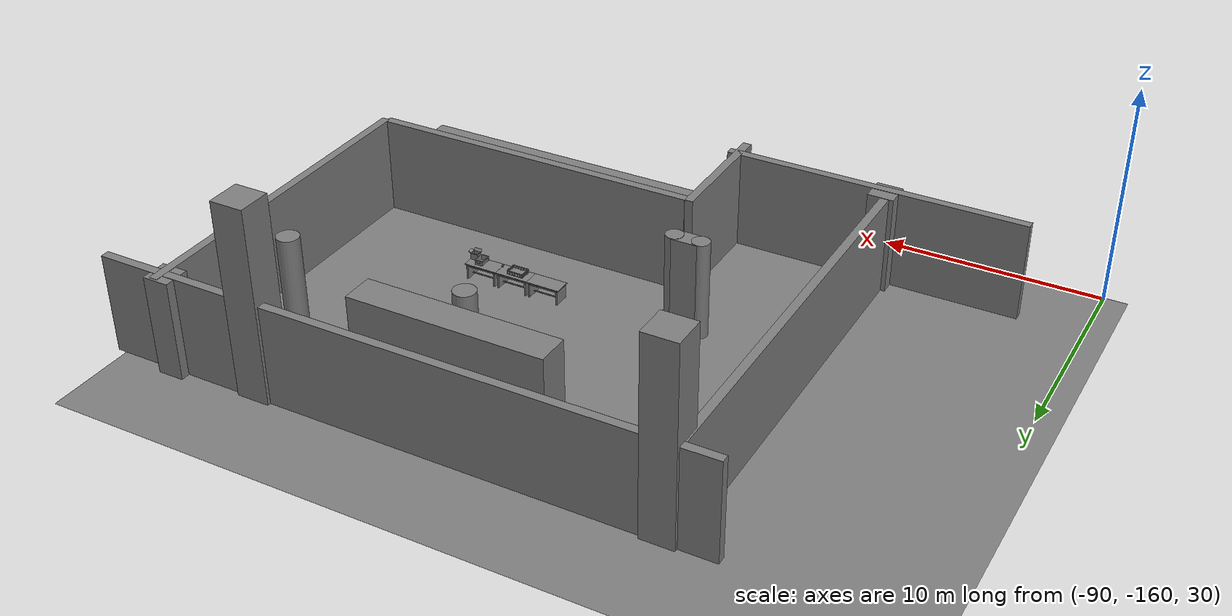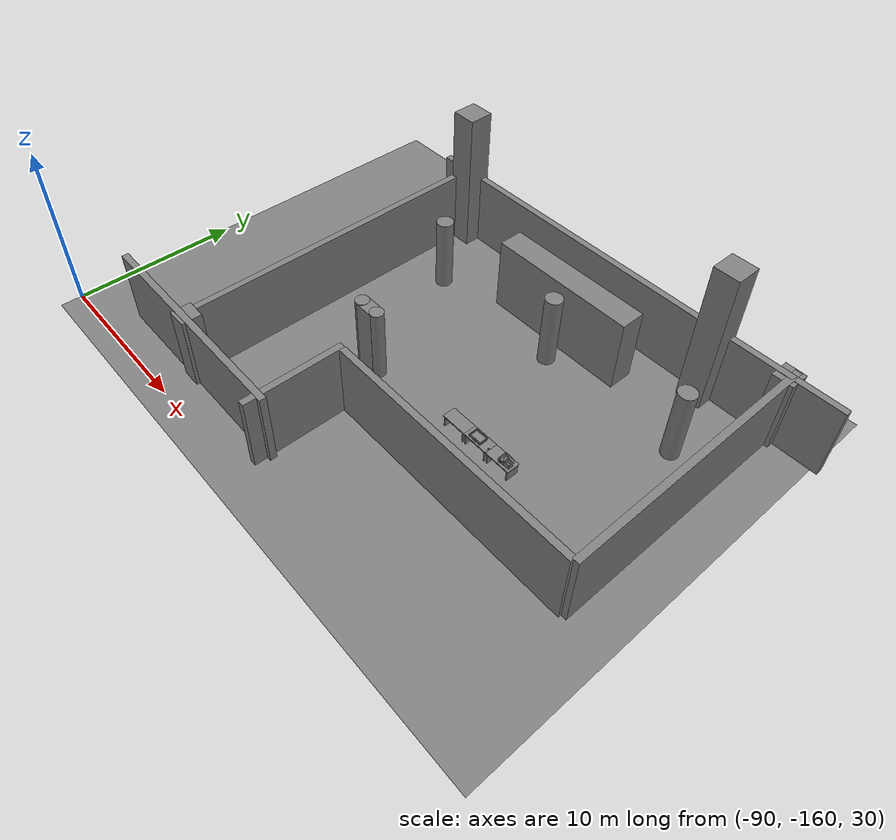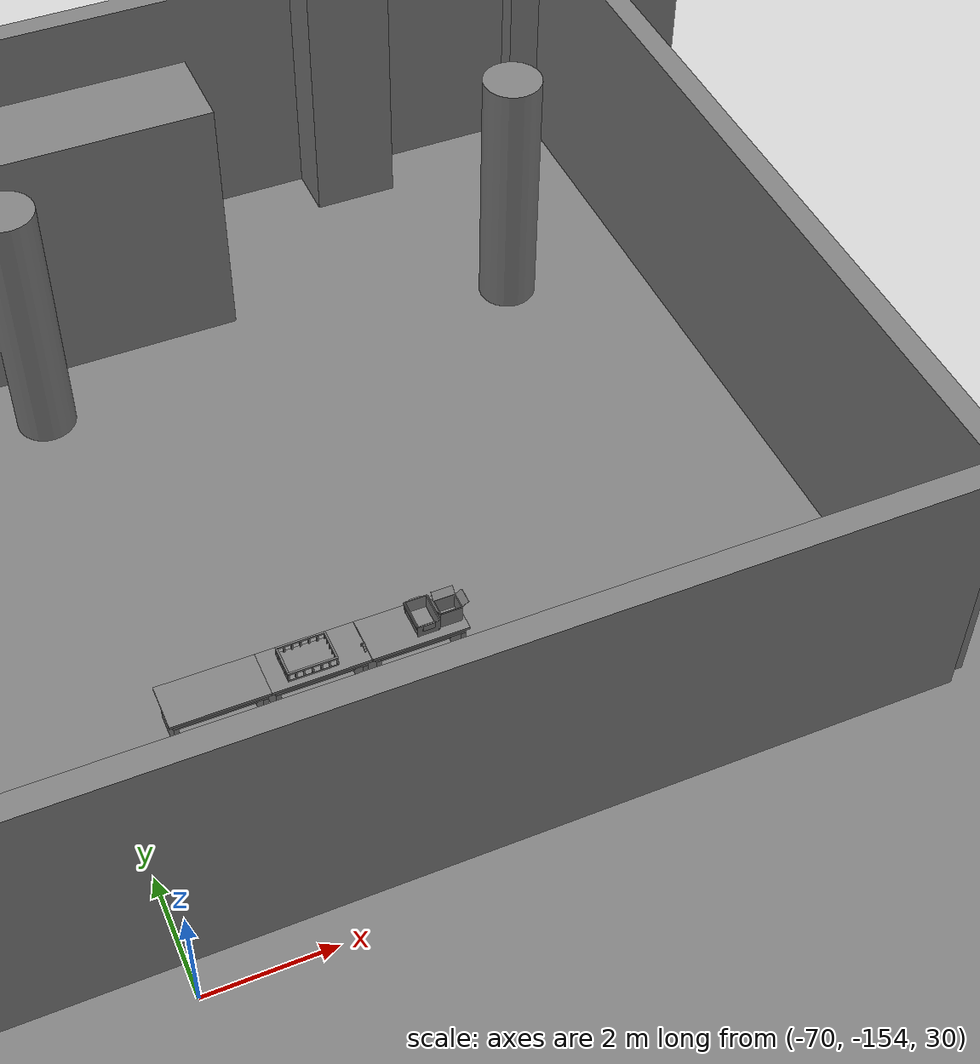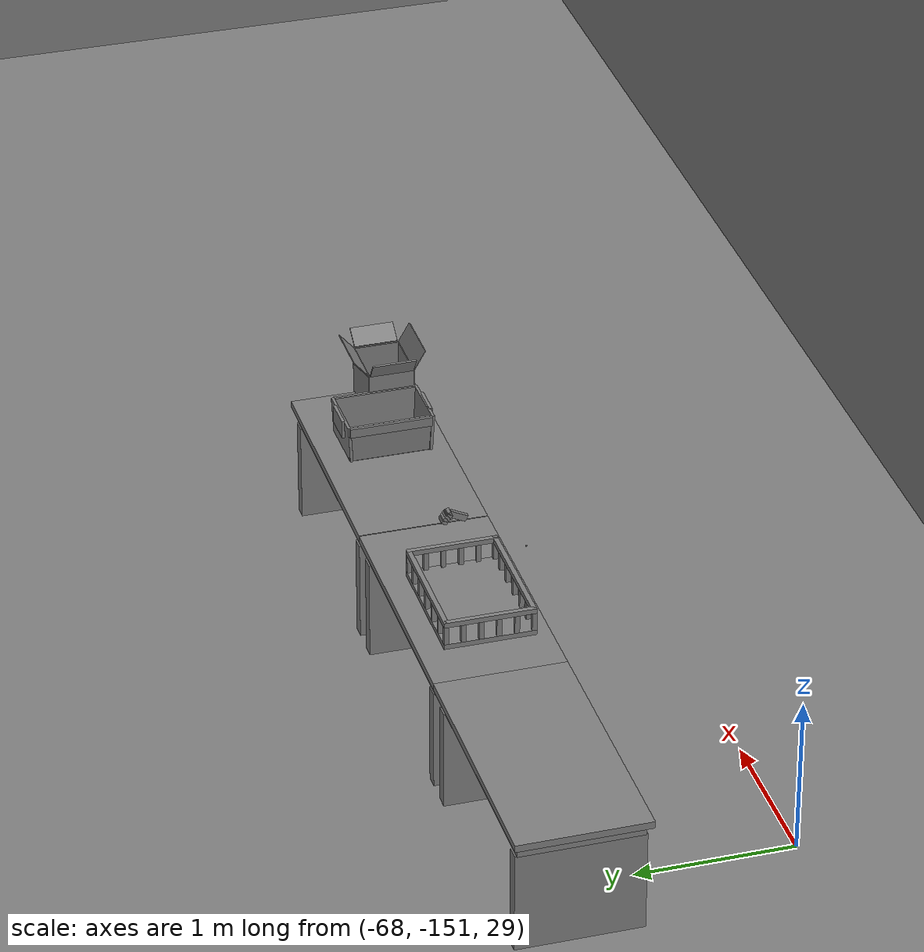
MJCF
<mujoco>
    <option gravity="0.000000000 0.000000000 -9.810000420" timestep="0.0049999999" integrator="implicitfast" density="1.225" viscosity="1.8000001e-05" noslip_iterations="10" iterations="100" sdf_iterations="50">
        <flag multiccd="disable"/>
    </option>
    <size memory="1000M"/>
    <compiler coordinate="local"/>
    <worldbody>
        <light cutoff="30" pos="0 1 1" dir="0 -1 -2"/>
        <light cutoff="30" pos="0 -1 1" dir="0 1 -2"/>
        <body pos="-64.866622925 -149.383972168 30.183746338" euler="89.999992371 89.999946594 0.000000000" name="openloong_gripper_2f85_fix_base_usda_bluebox_01">
            <geom contype="1" conaffinity="1" density="1000" type="box" material="" rgba="0.500000000 0.500000000 0.500000000 1.000000000" solimp="0.899999976 0.949999988 0.001000000" friction="1.000000000 0.005000000 0.000100000" solref="0.020000000 1.000000000" margin="0" condim="3" group="0" pos="0.276596069 0.187225342 0.000061035" quat="0.707107008 0.000077501 0.707106471 0.000077456" size="0.100000001 0.057999998 0.010000000" name="openloong_gripper_2f85_fix_base_usda_geom_F5576719_498F_4F7E_9DE7_3E337B97D9A4"/>
            <geom contype="1" conaffinity="1" density="1000" type="box" material="" rgba="0.500000000 0.500000000 0.500000000 1.000000000" solimp="0.899999976 0.949999988 0.001000000" friction="1.000000000 0.005000000 0.000100000" solref="0.020000000 1.000000000" margin="0" condim="3" group="0" pos="0.000000000 0.002883911 0.000000000" quat="1.000000000 0.000000000 0.000000000 0.000000000" size="0.254000008 0.003000000 0.172000006" name="openloong_gripper_2f85_fix_base_usda_geom_F831E203_9FAE_4EDF_94E7_ADCCE70CD584"/>
            <geom contype="1" conaffinity="1" density="1000" type="box" material="" rgba="0.500000000 0.500000000 0.500000000 1.000000000" solimp="0.899999976 0.949999988 0.001000000" friction="1.000000000 0.005000000 0.000100000" solref="0.020000000 1.000000000" margin="0" condim="3" group="0" pos="0.000015259 0.124874115 0.173477173" quat="0.999796450 0.020176515 -0.000000015 0.000000030" size="0.259999990 0.119999997 0.007000000" name="openloong_gripper_2f85_fix_base_usda_geom_5906FE80_700B_4262_A6DF_B3A3B3E5B4DC"/>
            <geom contype="1" conaffinity="1" density="1000" type="box" material="" rgba="0.500000000 0.500000000 0.500000000 1.000000000" solimp="0.899999976 0.949999988 0.001000000" friction="1.000000000 0.005000000 0.000100000" solref="0.020000000 1.000000000" margin="0" condim="3" group="0" pos="0.000015259 0.124874115 -0.173477173" quat="0.999796450 -0.020176545 -0.000000015 0.000000000" size="0.259999990 0.119999997 0.007000000" name="openloong_gripper_2f85_fix_base_usda_geom_D098E6C9_C113_4798_92B6_C7540359B3C0"/>
            <geom contype="1" conaffinity="1" density="1000" type="box" material="" rgba="0.500000000 0.500000000 0.500000000 1.000000000" solimp="0.899999976 0.949999988 0.001000000" friction="1.000000000 0.005000000 0.000100000" solref="0.020000000 1.000000000" margin="0" condim="3" group="0" pos="0.000015259 0.214012146 0.188980103" quat="0.999913096 0.013176724 0.000000015 0.000000000" size="0.259999990 0.029999999 0.012500000" name="openloong_gripper_2f85_fix_base_usda_geom_6B96EF35_C2B6_482C_9758_6B861CBCA8D9"/>
            <geom contype="1" conaffinity="1" density="1000" type="box" material="" rgba="0.500000000 0.500000000 0.500000000 1.000000000" solimp="0.899999976 0.949999988 0.001000000" friction="1.000000000 0.005000000 0.000100000" solref="0.020000000 1.000000000" margin="0" condim="3" group="0" pos="-0.258346558 0.125289917 0.001876831" quat="0.702796996 -0.020792052 0.710783184 0.020769238" size="0.189999998 0.119999997 0.009000000" name="openloong_gripper_2f85_fix_base_usda_geom_3F25D4FD_F42A_4A23_BFCE_8A8BA847AD7A"/>
            <geom contype="1" conaffinity="1" density="1000" type="box" material="" rgba="0.500000000 0.500000000 0.500000000 1.000000000" solimp="0.899999976 0.949999988 0.001000000" friction="1.000000000 0.005000000 0.000100000" solref="0.020000000 1.000000000" margin="0" condim="3" group="0" pos="0.000015259 0.214012146 -0.188980103" quat="0.999913096 -0.013176769 0.000000030 0.000000015" size="0.259999990 0.029999999 0.012500000" name="openloong_gripper_2f85_fix_base_usda_geom_908FF0E1_E51F_4A27_991C_2C52A398DA2F"/>
            <geom contype="1" conaffinity="1" density="1000" type="box" material="" rgba="0.500000000 0.500000000 0.500000000 1.000000000" solimp="0.899999976 0.949999988 0.001000000" friction="1.000000000 0.005000000 0.000100000" solref="0.020000000 1.000000000" margin="0" condim="3" group="0" pos="-0.276596069 0.187225342 0.000061035" quat="0.707106650 0.000077441 0.707106709 0.000077456" size="0.100000001 0.057999998 0.010000000" name="openloong_gripper_2f85_fix_base_usda_geom_5F5EEA6B_FF80_4109_9B5C_C1259A26E5BD"/>
            <geom contype="1" conaffinity="1" density="1000" type="box" material="" rgba="0.500000000 0.500000000 0.500000000 1.000000000" solimp="0.899999976 0.949999988 0.001000000" friction="1.000000000 0.005000000 0.000100000" solref="0.020000000 1.000000000" margin="0" condim="3" group="0" pos="0.258346558 0.125289917 0.001876831" quat="0.702851534 0.018856451 0.710823834 -0.019329429" size="0.189999998 0.119999997 0.009000000" name="openloong_gripper_2f85_fix_base_usda_geom_36CDEE3D_3632_422B_99D2_324A30301E89"/>
            <freejoint name="openloong_gripper_2f85_fix_base_usda_bluebox_01_joint"/>
            <site size="0.005000000 0.005000000 0.005000000" rgba="0.500000000 0.500000000 0.500000000 1.000000000" pos="0.000000000 0.000000000 0.000000000" quat="0.999961913 0.008726534 0.000000000 0.000000000" group="0" type="sphere" name="openloong_gripper_2f85_fix_base_usda_bluebox_01site"/>
        </body>
        <body pos="-64.496299744 -149.491867065 30.235729218" euler="0.000000000 0.000000000 89.999946594" name="openloong_gripper_2f85_fix_base_usda_cardboardbox_01">
            <geom contype="1" conaffinity="1" density="1000" type="box" material="" rgba="0.500000000 0.500000000 0.500000000 1.000000000" solimp="0.899999976 0.949999988 0.001000000" friction="1.000000000 0.005000000 0.000100000" solref="0.020000000 1.000000000" margin="0" condim="3" group="0" pos="-0.003166199 -0.004086494 0.005052090" quat="1.000000000 0.000000000 0.000000000 0.000000000" size="0.142499998 0.177500010 0.005000000" name="openloong_gripper_2f85_fix_base_usda_geom_32897504_E338_4B71_AF45_A3874E2FB109"/>
            <geom contype="1" conaffinity="1" density="1000" type="box" material="" rgba="0.500000000 0.500000000 0.500000000 1.000000000" solimp="0.899999976 0.949999988 0.001000000" friction="1.000000000 0.005000000 0.000100000" solref="0.020000000 1.000000000" margin="0" condim="3" group="0" pos="-0.003166199 0.170316696 0.150570869" quat="1.000000000 0.000000000 0.000000000 0.000000000" size="0.142499998 0.005000000 0.149999991" name="openloong_gripper_2f85_fix_base_usda_geom_9D43E240_CBD5_49BC_9462_7057859795DD"/>
            <geom contype="1" conaffinity="1" density="1000" type="box" material="" rgba="0.500000000 0.500000000 0.500000000 1.000000000" solimp="0.899999976 0.949999988 0.001000000" friction="1.000000000 0.005000000 0.000100000" solref="0.020000000 1.000000000" margin="0" condim="3" group="0" pos="-0.147399902 -0.005307198 0.150570869" quat="1.000000000 0.000000000 0.000000000 0.000000000" size="0.005000000 0.177500010 0.149999991" name="openloong_gripper_2f85_fix_base_usda_geom_7C05172B_6AD2_4FAD_99C8_ECC323F28EC1"/>
            <geom contype="1" conaffinity="1" density="1000" type="box" material="" rgba="0.500000000 0.500000000 0.500000000 1.000000000" solimp="0.899999976 0.949999988 0.001000000" friction="1.000000000 0.005000000 0.000100000" solref="0.020000000 1.000000000" margin="0" condim="3" group="0" pos="0.140275955 -0.005307198 0.150570869" quat="1.000000000 0.000000000 0.000000000 0.000000000" size="0.005000000 0.177500010 0.149999991" name="openloong_gripper_2f85_fix_base_usda_geom_B4A6F4A6_25C8_4FF7_9852_F8B743EBCB0A"/>
            <geom contype="1" conaffinity="1" density="1000" type="box" material="" rgba="0.500000000 0.500000000 0.500000000 1.000000000" solimp="0.899999976 0.949999988 0.001000000" friction="1.000000000 0.005000000 0.000100000" solref="0.020000000 1.000000000" margin="0" condim="3" group="0" pos="-0.003166199 -0.181550980 0.150570869" quat="1.000000000 0.000000000 0.000000000 0.000000000" size="0.142499998 0.005000000 0.149999991" name="openloong_gripper_2f85_fix_base_usda_geom_9D6A641D_234C_4807_ABCC_54695DD4C333"/>
            <freejoint name="openloong_gripper_2f85_fix_base_usda_cardboardbox_01_joint"/>
            <site size="0.005000000 0.005000000 0.005000000" rgba="0.500000000 0.500000000 0.500000000 1.000000000" pos="0.000000000 0.000000000 0.000000000" quat="0.999961913 0.008726535 0.000000000 0.000000000" group="0" type="sphere" name="openloong_gripper_2f85_fix_base_usda_site_F6997831_5155_4C79_8EE3_CC6CC86610DA"/>
            <body pos="0.139160156 -0.004048347 0.301930904" euler="-179.999954224 49.383502960 179.999954224" name="openloong_gripper_2f85_fix_base_usda_A1_006">
                <geom contype="1" conaffinity="1" density="1000" type="box" material="" rgba="0.500000000 0.500000000 0.500000000 1.000000000" solimp="0.899999976 0.949999988 0.001000000" friction="1.000000000 0.005000000 0.000100000" solref="0.020000000 1.000000000" margin="0" condim="3" group="0" pos="-0.071587563 0.000009537 0.001745224" quat="0.999999881 0.000000000 0.000000000 0.000000000" size="0.071249999 0.179999992 0.002500000" name="openloong_gripper_2f85_fix_base_usda_geom_FDAD4613_2D72_493D_B610_9B7B42047D7E"/>
                <joint armature="0" stiffness="0.07" damping="0.0099999998" axis="0.000000 1.000000 0.000000" type="hinge" name="openloong_gripper_2f85_fix_base_usda_A1_006"/>
            </body>
            <body pos="-0.145902634 -0.004086494 0.301938057" euler="-180.000000000 -60.000011444 -180.000000000" name="openloong_gripper_2f85_fix_base_usda_A2_006">
                <geom contype="1" conaffinity="1" density="1000" type="box" material="" rgba="0.500000000 0.500000000 0.500000000 1.000000000" solimp="0.899999976 0.949999988 0.001000000" friction="1.000000000 0.005000000 0.000100000" solref="0.020000000 1.000000000" margin="0" condim="3" group="0" pos="0.071268082 0.000009537 0.002717972" quat="0.000002921 0.000000000 -0.000000030 0.999999881" size="0.071249999 0.179999992 0.002500000" name="openloong_gripper_2f85_fix_base_usda_geom_C6482447_E3FD_47D2_823D_AF624635E722"/>
                <joint armature="0" stiffness="0.07" damping="0.0099999998" axis="0.000000 1.000000 0.000000" type="hinge" name="openloong_gripper_2f85_fix_base_usda_A2_006"/>
            </body>
            <body pos="-0.003385544 0.175991058 0.301930904" euler="-125.858116150 -0.000004561 0.000002331" name="openloong_gripper_2f85_fix_base_usda_B2_006">
                <geom contype="1" conaffinity="1" density="1000" type="box" material="" rgba="0.500000000 0.500000000 0.500000000 1.000000000" solimp="0.899999976 0.949999988 0.001000000" friction="1.000000000 0.005000000 0.000100000" solref="0.020000000 1.000000000" margin="0" condim="3" group="0" pos="0.000009537 -0.070939064 -0.002470016" quat="0.999614120 0.027776197 -0.000000015 0.000000030" size="0.137500003 0.064999998 0.005000000" name="openloong_gripper_2f85_fix_base_usda_geom_B328773B_F2CE_4F09_9989_6697B0A27FD3"/>
                <joint armature="0" stiffness="0.07" damping="0.0099999998" axis="1.000000 0.000000 0.000000" type="hinge" name="openloong_gripper_2f85_fix_base_usda_B2_006"/>
            </body>
            <body pos="-0.003385544 -0.184140205 0.301938057" euler="147.805557251 0.000000000 0.000000000" name="openloong_gripper_2f85_fix_base_usda_B1_006">
                <geom contype="1" conaffinity="1" density="1000" type="box" material="" rgba="0.500000000 0.500000000 0.500000000 1.000000000" solimp="0.899999976 0.949999988 0.001000000" friction="1.000000000 0.005000000 0.000100000" solref="0.020000000 1.000000000" margin="0" condim="3" group="0" pos="-0.000028610 0.070202351 -0.002703667" quat="0.999614179 -0.027776167 0.000000000 0.000000000" size="0.137500003 0.064999998 0.005000000" name="openloong_gripper_2f85_fix_base_usda_geom_48C606A4_9D0F_4CCD_A375_B75E07A1A26D"/>
                <joint armature="0" stiffness="0.07" damping="0.0099999998" axis="1.000000 0.000000 0.000000" type="hinge" name="openloong_gripper_2f85_fix_base_usda_B1_006"/>
            </body>
        </body>
        <body pos="-65.882858276 -149.481979370 30.229999542" euler="-64.487716675 0.000000000 0.000000000" name="openloong_gripper_2f85_fix_base_usda_Barcode">
            <geom contype="1" conaffinity="1" density="1000" type="box" material="" rgba="0.500000000 0.500000000 0.500000000 1.000000000" solimp="0.899999976 0.949999988 0.001000000" friction="1.000000000 0.005000000 0.000100000" solref="0.020000000 1.000000000" margin="0" condim="3" group="0" pos="0.000000000 0.013038635 0.001419067" quat="0.000000000 0.000000000 0.000000000 1.000000119" size="0.034000002 0.010000000 0.017999999" name="openloong_gripper_2f85_fix_base_usda_geom_337B09BD_528D_4A60_9E08_576ADD553922"/>
            <geom contype="1" conaffinity="1" density="1000" type="box" material="" rgba="0.500000000 0.500000000 0.500000000 1.000000000" solimp="0.899999976 0.949999988 0.001000000" friction="1.000000000 0.005000000 0.000100000" solref="0.020000000 1.000000000" margin="0" condim="3" group="0" pos="0.000000000 -0.035301208 -0.007095337" quat="0.000000000 0.000000000 -0.043619365 0.999048233" size="0.028999999 0.010000000 0.020000000" name="openloong_gripper_2f85_fix_base_usda_geom_BD24754A_11CF_410E_9B42_B72E3FD6C9F7"/>
            <geom contype="1" conaffinity="1" density="1000" type="box" material="" rgba="0.500000000 0.500000000 0.500000000 1.000000000" solimp="0.899999976 0.949999988 0.001000000" friction="1.000000000 0.005000000 0.000100000" solref="0.020000000 1.000000000" margin="0" condim="3" group="0" pos="0.000000000 -0.043411255 -0.011749268" quat="0.922262907 0.386563420 0.000000000 0.000000000" size="0.026000001 0.010000000 0.020000000" name="openloong_gripper_2f85_fix_base_usda_geom_BA0B282C_74C8_4236_A242_C59BDF170A17"/>
            <geom contype="1" conaffinity="1" density="1000" type="box" material="" rgba="0.500000000 0.500000000 0.500000000 1.000000000" solimp="0.899999976 0.949999988 0.001000000" friction="1.000000000 0.005000000 0.000100000" solref="0.020000000 1.000000000" margin="0" condim="3" group="0" pos="0.000000000 -0.016967773 -0.031860352" quat="0.000000000 0.000000000 0.000000000 1.000000119" size="0.008000000 0.010000000 0.013000000" name="openloong_gripper_2f85_fix_base_usda_geom_B328D1C4_C025_48E9_A41B_981AF1FE7C23"/>
            <geom contype="1" conaffinity="1" density="1000" type="box" material="" rgba="0.500000000 0.500000000 0.500000000 1.000000000" solimp="0.899999976 0.949999988 0.001000000" friction="1.000000000 0.005000000 0.000100000" solref="0.020000000 1.000000000" margin="0" condim="3" group="0" pos="0.000000000 -0.001869202 0.000312805" quat="0.953716993 0.300705761 0.000000000 0.000000000" size="0.032000002 0.010000000 0.018999999" name="openloong_gripper_2f85_fix_base_usda_geom_45515688_FE79_4408_B6BF_92C5ED39BC61"/>
            <geom contype="1" conaffinity="1" density="1000" type="box" material="" rgba="0.500000000 0.500000000 0.500000000 1.000000000" solimp="0.899999976 0.949999988 0.001000000" friction="1.000000000 0.005000000 0.000100000" solref="0.020000000 1.000000000" margin="0" condim="3" group="0" pos="0.000000000 -0.019531250 -0.003173828" quat="0.953716993 0.300705761 0.000000000 0.000000000" size="0.030999999 0.010000000 0.020000000" name="openloong_gripper_2f85_fix_base_usda_geom_B47CD103_F962_447F_AD5C_D4F1DF9ED679"/>
            <geom contype="1" conaffinity="1" density="1000" type="box" material="" rgba="0.500000000 0.500000000 0.500000000 1.000000000" solimp="0.899999976 0.949999988 0.001000000" friction="1.000000000 0.005000000 0.000100000" solref="0.020000000 1.000000000" margin="0" condim="3" group="0" pos="0.000000000 -0.035301208 -0.007095337" quat="0.953716993 0.300705761 0.000000000 0.000000000" size="0.028999999 0.010000000 0.020000000" name="openloong_gripper_2f85_fix_base_usda_geom_F79328CA_BC5C_4F4A_9563_E18E74186A1C"/>
            <geom contype="1" conaffinity="1" density="1000" type="box" material="" rgba="0.500000000 0.500000000 0.500000000 1.000000000" solimp="0.899999976 0.949999988 0.001000000" friction="1.000000000 0.005000000 0.000100000" solref="0.020000000 1.000000000" margin="0" condim="3" group="0" pos="0.000000000 -0.042617798 -0.071121216" quat="0.000000000 0.000000000 0.000000000 1.000000119" size="0.013000000 0.021000000 0.059999999" name="openloong_gripper_2f85_fix_base_usda_geom_2069C85E_F055_480C_B68B_A346F18881CC"/>
            <freejoint name="openloong_gripper_2f85_fix_base_usda_Barcode_joint"/>
            <site size="0.005000000 0.005000000 0.005000000" rgba="0.500000000 0.500000000 0.500000000 1.000000000" pos="0.000000000 0.000000000 0.000000000" quat="1.000000000 0.000000000 0.000000000 0.000000000" group="0" type="sphere" name="openloong_gripper_2f85_fix_base_usda_Barcode_site"/>
        </body>
        <body pos="-66.745018005 -149.392349243 30.184000015" euler="0.000000000 0.000000000 89.999946594" name="[22332893610708]_Basket_01">
            <geom contype="1" conaffinity="1" density="1000" type="box" material="" rgba="0.500000000 0.500000000 0.500000000 1.000000000" solimp="0.899999976 0.949999988 0.001000000" friction="1.000000000 0.005000000 0.000100000" solref="0.020000000 1.000000000" margin="0" condim="3" group="0" pos="-0.052425385 0.389207840 0.089787483" quat="0.707107008 0.000000000 0.000000000 0.707106411" size="0.014249999 0.014249999 0.059999999" name="[22332893610708]_geom_F1D45228_74EF_4C52_A720_3FA135717EA2"/>
            <geom contype="1" conaffinity="1" density="1000" type="box" material="" rgba="0.500000000 0.500000000 0.500000000 1.000000000" solimp="0.899999976 0.949999988 0.001000000" friction="1.000000000 0.005000000 0.000100000" solref="0.020000000 1.000000000" margin="0" condim="3" group="0" pos="0.264015198 -0.133043289 0.089787483" quat="0.707107008 0.000000000 0.000000000 0.707106411" size="0.014249999 0.014249999 0.059999999" name="[22332893610708]_geom_A595ED80_933F_45A0_B0CB_03C209A067D7"/>
            <geom contype="1" conaffinity="1" density="1000" type="box" material="" rgba="0.500000000 0.500000000 0.500000000 1.000000000" solimp="0.899999976 0.949999988 0.001000000" friction="1.000000000 0.005000000 0.000100000" solref="0.020000000 1.000000000" margin="0" condim="3" group="0" pos="-0.264015198 -0.265548706 0.089793205" quat="0.707107008 0.000000000 0.000000000 0.707106411" size="0.014249999 0.014249999 0.059999999" name="[22332893610708]_geom_1468F332_94D9_4062_A0B0_FAEED3B9943E"/>
            <geom contype="1" conaffinity="1" density="1000" type="box" material="" rgba="0.500000000 0.500000000 0.500000000 1.000000000" solimp="0.899999976 0.949999988 0.001000000" friction="1.000000000 0.005000000 0.000100000" solref="0.020000000 1.000000000" margin="0" condim="3" group="0" pos="-0.160263062 -0.389322281 0.089793205" quat="0.707107008 0.000000000 0.000000000 0.707106411" size="0.014249999 0.014249999 0.059999999" name="[22332893610708]_geom_1762C867_82F5_4157_9B63_F2626686671D"/>
            <geom contype="1" conaffinity="1" density="1000" type="box" material="" rgba="0.500000000 0.500000000 0.500000000 1.000000000" solimp="0.899999976 0.949999988 0.001000000" friction="1.000000000 0.005000000 0.000100000" solref="0.020000000 1.000000000" margin="0" condim="3" group="0" pos="0.162265778 -0.389322281 0.089787483" quat="0.707107008 0.000000000 0.000000000 0.707106411" size="0.014249999 0.014249999 0.059999999" name="[22332893610708]_geom_93362EED_E926_4360_837E_C6133F17A426"/>
            <geom contype="1" conaffinity="1" density="1000" type="box" material="" rgba="0.500000000 0.500000000 0.500000000 1.000000000" solimp="0.899999976 0.949999988 0.001000000" friction="1.000000000 0.005000000 0.000100000" solref="0.020000000 1.000000000" margin="0" condim="3" group="0" pos="0.264015198 0.389207840 0.089787483" quat="0.707107008 0.000000000 0.000000000 0.707106411" size="0.014249999 0.014249999 0.059999999" name="[22332893610708]_geom_87A7B91B_256A_4FF8_9341_78E26E553C94"/>
            <geom contype="1" conaffinity="1" density="1000" type="box" material="" rgba="0.500000000 0.500000000 0.500000000 1.000000000" solimp="0.899999976 0.949999988 0.001000000" friction="1.000000000 0.005000000 0.000100000" solref="0.020000000 1.000000000" margin="0" condim="3" group="0" pos="-0.264015198 -0.133043289 0.089793205" quat="0.707107008 0.000000000 0.000000000 0.707106411" size="0.014249999 0.014249999 0.059999999" name="[22332893610708]_geom_3E4910FC_3210_4C56_947C_DE6055DEAC26"/>
            <geom contype="1" conaffinity="1" density="1000" type="box" material="" rgba="0.500000000 0.500000000 0.500000000 1.000000000" solimp="0.899999976 0.949999988 0.001000000" friction="1.000000000 0.005000000 0.000100000" solref="0.020000000 1.000000000" margin="0" condim="3" group="0" pos="-0.264026642 0.269256592 0.089793205" quat="0.707107008 0.000000000 0.000000000 0.707106411" size="0.014249999 0.014249999 0.059999999" name="[22332893610708]_geom_76562EE0_F332_4677_BB94_FA74E4431862"/>
            <geom contype="1" conaffinity="1" density="1000" type="box" material="" rgba="0.500000000 0.500000000 0.500000000 1.000000000" solimp="0.899999976 0.949999988 0.001000000" friction="1.000000000 0.005000000 0.000100000" solref="0.020000000 1.000000000" margin="0" condim="3" group="0" pos="0.054462433 0.389207840 0.089787483" quat="0.707107008 0.000000000 0.000000000 0.707106411" size="0.014249999 0.014249999 0.059999999" name="[22332893610708]_geom_2206D6DA_086C_4895_8BD4_001D35D16926"/>
            <geom contype="1" conaffinity="1" density="1000" type="box" material="" rgba="0.500000000 0.500000000 0.500000000 1.000000000" solimp="0.899999976 0.949999988 0.001000000" friction="1.000000000 0.005000000 0.000100000" solref="0.020000000 1.000000000" margin="0" condim="3" group="0" pos="0.054462433 -0.389322281 0.089787483" quat="0.707107008 0.000000000 0.000000000 0.707106411" size="0.014249999 0.014249999 0.059999999" name="[22332893610708]_geom_0009DB6E_CF79_4C06_8C15_41F241E3AE47"/>
            <geom contype="1" conaffinity="1" density="1000" type="box" material="" rgba="0.500000000 0.500000000 0.500000000 1.000000000" solimp="0.899999976 0.949999988 0.001000000" friction="1.000000000 0.005000000 0.000100000" solref="0.020000000 1.000000000" margin="0" condim="3" group="0" pos="0.264015198 0.269256592 0.089793205" quat="0.707107008 0.000000000 0.000000000 0.707106411" size="0.014249999 0.014249999 0.059999999" name="[22332893610708]_geom_EAEB0518_A574_4D52_82ED_FE381FDC6F3C"/>
            <geom contype="1" conaffinity="1" density="1000" type="box" material="" rgba="0.500000000 0.500000000 0.500000000 1.000000000" solimp="0.899999976 0.949999988 0.001000000" friction="1.000000000 0.005000000 0.000100000" solref="0.020000000 1.000000000" margin="0" condim="3" group="0" pos="0.264015198 -0.389322281 0.089787483" quat="0.707107008 0.000000000 0.000000000 0.707106411" size="0.014249999 0.014249999 0.059999999" name="[22332893610708]_geom_E57C392E_6C02_45A2_9FE4_5AA46296E510"/>
            <geom contype="1" conaffinity="1" density="1000" type="box" material="" rgba="0.500000000 0.500000000 0.500000000 1.000000000" solimp="0.899999976 0.949999988 0.001000000" friction="1.000000000 0.005000000 0.000100000" solref="0.020000000 1.000000000" margin="0" condim="3" group="0" pos="0.000000000 0.000000000 0.015998840" quat="0.707107008 0.000000000 0.000000000 0.707106411" size="0.403499991 0.279000014 0.015750000" name="[22332893610708]_geom_9A14BE58_FD5C_4DCF_A1BF_09BD244155B3"/>
            <geom contype="1" conaffinity="1" density="1000" type="box" material="" rgba="0.500000000 0.500000000 0.500000000 1.000000000" solimp="0.899999976 0.949999988 0.001000000" friction="1.000000000 0.005000000 0.000100000" solref="0.020000000 1.000000000" margin="0" condim="3" group="0" pos="0.000000000 -0.389476776 0.163619041" quat="0.707107008 0.000000000 0.000000000 0.707106411" size="0.015000000 0.277500004 0.015750000" name="[22332893610708]_geom_7416D7F2_A647_457D_9DAD_F32486A1B972"/>
            <geom contype="1" conaffinity="1" density="1000" type="box" material="" rgba="0.500000000 0.500000000 0.500000000 1.000000000" solimp="0.899999976 0.949999988 0.001000000" friction="1.000000000 0.005000000 0.000100000" solref="0.020000000 1.000000000" margin="0" condim="3" group="0" pos="0.162265778 0.389207840 0.089787483" quat="0.707107008 0.000000000 0.000000000 0.707106411" size="0.014249999 0.014249999 0.059999999" name="[22332893610708]_geom_DE8D6AA5_F658_4177_BF87_9F951D534AE4"/>
            <geom contype="1" conaffinity="1" density="1000" type="box" material="" rgba="0.500000000 0.500000000 0.500000000 1.000000000" solimp="0.899999976 0.949999988 0.001000000" friction="1.000000000 0.005000000 0.000100000" solref="0.020000000 1.000000000" margin="0" condim="3" group="0" pos="0.000000000 0.389471054 0.163619041" quat="0.707107008 0.000000000 0.000000000 0.707106411" size="0.015000000 0.277500004 0.015750000" name="[22332893610708]_geom_89801695_DE20_45E4_BE1D_26474C334348"/>
            <geom contype="1" conaffinity="1" density="1000" type="box" material="" rgba="0.500000000 0.500000000 0.500000000 1.000000000" solimp="0.899999976 0.949999988 0.001000000" friction="1.000000000 0.005000000 0.000100000" solref="0.020000000 1.000000000" margin="0" condim="3" group="0" pos="-0.263511658 0.000000000 0.163619041" quat="0.707107008 0.000000000 0.000000000 0.707106411" size="0.403499991 0.015000000 0.015750000" name="[22332893610708]_geom_4AA55F3A_B353_4F99_A47A_29868B682FF7"/>
            <geom contype="1" conaffinity="1" density="1000" type="box" material="" rgba="0.500000000 0.500000000 0.500000000 1.000000000" solimp="0.899999976 0.949999988 0.001000000" friction="1.000000000 0.005000000 0.000100000" solref="0.020000000 1.000000000" margin="0" condim="3" group="0" pos="-0.264015198 0.141334534 0.089793205" quat="0.707107008 0.000000000 0.000000000 0.707106411" size="0.014249999 0.014249999 0.059999999" name="[22332893610708]_geom_A1170965_D636_46E7_8423_6C6A3B775458"/>
            <geom contype="1" conaffinity="1" density="1000" type="box" material="" rgba="0.500000000 0.500000000 0.500000000 1.000000000" solimp="0.899999976 0.949999988 0.001000000" friction="1.000000000 0.005000000 0.000100000" solref="0.020000000 1.000000000" margin="0" condim="3" group="0" pos="0.264015198 -0.265548706 0.089787483" quat="0.707107008 0.000000000 0.000000000 0.707106411" size="0.014249999 0.014249999 0.059999999" name="[22332893610708]_geom_9A4575D6_3096_428F_9303_C8365428D65A"/>
            <geom contype="1" conaffinity="1" density="1000" type="box" material="" rgba="0.500000000 0.500000000 0.500000000 1.000000000" solimp="0.899999976 0.949999988 0.001000000" friction="1.000000000 0.005000000 0.000100000" solref="0.020000000 1.000000000" margin="0" condim="3" group="0" pos="-0.160263062 0.389207840 0.089787483" quat="0.707107008 0.000000000 0.000000000 0.707106411" size="0.014249999 0.014249999 0.059999999" name="[22332893610708]_geom_55047696_434C_46E6_9264_7A32698542C0"/>
            <geom contype="1" conaffinity="1" density="1000" type="box" material="" rgba="0.500000000 0.500000000 0.500000000 1.000000000" solimp="0.899999976 0.949999988 0.001000000" friction="1.000000000 0.005000000 0.000100000" solref="0.020000000 1.000000000" margin="0" condim="3" group="0" pos="-0.052425385 -0.389322281 0.089787483" quat="0.707107008 0.000000000 0.000000000 0.707106411" size="0.014249999 0.014249999 0.059999999" name="[22332893610708]_geom_8DCAB951_3794_4F99_A4A0_A3FF1E206F86"/>
            <geom contype="1" conaffinity="1" density="1000" type="box" material="" rgba="0.500000000 0.500000000 0.500000000 1.000000000" solimp="0.899999976 0.949999988 0.001000000" friction="1.000000000 0.005000000 0.000100000" solref="0.020000000 1.000000000" margin="0" condim="3" group="0" pos="-0.264026642 -0.389322281 0.089793205" quat="0.707107008 0.000000000 0.000000000 0.707106411" size="0.014249999 0.014249999 0.059999999" name="[22332893610708]_geom_E3D42AF5_E3F4_4F58_8972_19AD148A6AFF"/>
            <geom contype="1" conaffinity="1" density="1000" type="box" material="" rgba="0.500000000 0.500000000 0.500000000 1.000000000" solimp="0.899999976 0.949999988 0.001000000" friction="1.000000000 0.005000000 0.000100000" solref="0.020000000 1.000000000" margin="0" condim="3" group="0" pos="0.264015198 0.141334534 0.089787483" quat="0.707107008 0.000000000 0.000000000 0.707106411" size="0.014249999 0.014249999 0.059999999" name="[22332893610708]_geom_D3D9B5FB_F41B_4ABA_BF0A_D58C53609A6C"/>
            <geom contype="1" conaffinity="1" density="1000" type="box" material="" rgba="0.500000000 0.500000000 0.500000000 1.000000000" solimp="0.899999976 0.949999988 0.001000000" friction="1.000000000 0.005000000 0.000100000" solref="0.020000000 1.000000000" margin="0" condim="3" group="0" pos="-0.264015198 0.389207840 0.089793205" quat="0.707107008 0.000000000 0.000000000 0.707106411" size="0.014249999 0.014249999 0.059999999" name="[22332893610708]_geom_E80D53E5_7B82_482B_8FED_C67CBE420DC2"/>
            <geom contype="1" conaffinity="1" density="1000" type="box" material="" rgba="0.500000000 0.500000000 0.500000000 1.000000000" solimp="0.899999976 0.949999988 0.001000000" friction="1.000000000 0.005000000 0.000100000" solref="0.020000000 1.000000000" margin="0" condim="3" group="0" pos="0.264015198 0.004480362 0.089787483" quat="0.707107008 0.000000000 0.000000000 0.707106411" size="0.014249999 0.014249999 0.059999999" name="[22332893610708]_geom_AAFC508D_59A1_449B_82CF_2E7EF67DEA04"/>
            <geom contype="1" conaffinity="1" density="1000" type="box" material="" rgba="0.500000000 0.500000000 0.500000000 1.000000000" solimp="0.899999976 0.949999988 0.001000000" friction="1.000000000 0.005000000 0.000100000" solref="0.020000000 1.000000000" margin="0" condim="3" group="0" pos="0.263694763 -0.000011444 0.163619041" quat="0.707107008 0.000000000 0.000000000 0.707106411" size="0.403499991 0.015000000 0.015750000" name="[22332893610708]_geom_EDE8498A_0EF2_4334_AEE6_BA37C8C977DC"/>
            <geom contype="1" conaffinity="1" density="1000" type="box" material="" rgba="0.500000000 0.500000000 0.500000000 1.000000000" solimp="0.899999976 0.949999988 0.001000000" friction="1.000000000 0.005000000 0.000100000" solref="0.020000000 1.000000000" margin="0" condim="3" group="0" pos="-0.264015198 0.004480362 0.089793205" quat="0.707107008 0.000000000 0.000000000 0.707106411" size="0.014249999 0.014249999 0.059999999" name="[22332893610708]_geom_64E27C24_CC5F_4F43_A0FB_833C34E667A4"/>
            <freejoint name="[22332893610708]_joint_CF756C16_3349_4CA1_9554_93DBE5BFBAD3"/>
        </body>
        <body pos="0.000000000 0.000000000 0.000000000" euler="0.000000000 0.000000000 0.000000000" name="Static Objects_Static Objects">
            <geom contype="1" conaffinity="1" density="1000" type="box" material="" rgba="0.500000000 0.500000000 0.500000000 1.000000000" solimp="0.899999976 0.949999988 0.001000000" friction="1.000000000 0.005000000 0.000100000" solref="0.020000000 1.000000000" margin="0" condim="3" group="0" pos="-67.544113159 -149.365814209 29.727830887" quat="0.500000417 0.499999970 0.499999553 0.499999970" size="0.381000012 0.319999993 0.041000001" name="Static Objects_geom_F23130D8_AFD8_48C9_9114_82B3BE62B461"/>
            <geom contype="1" conaffinity="1" density="1000" type="box" material="" rgba="0.500000000 0.500000000 0.500000000 1.000000000" solimp="0.899999976 0.949999988 0.001000000" friction="1.000000000 0.005000000 0.000100000" solref="0.020000000 1.000000000" margin="0" condim="3" group="0" pos="-68.239501953 -149.365814209 30.086868286" quat="0.500000417 0.499999970 0.499999553 0.499999970" size="0.370999992 0.039500002 0.745000005" name="Static Objects_geom_758831D7_F028_4B47_8D6F_4A5C83887395"/>
            <geom contype="1" conaffinity="1" density="1000" type="box" material="" rgba="0.500000000 0.500000000 0.500000000 1.000000000" solimp="0.899999976 0.949999988 0.001000000" friction="1.000000000 0.005000000 0.000100000" solref="0.020000000 1.000000000" margin="0" condim="3" group="0" pos="-68.239501953 -149.365814209 30.147235870" quat="0.500000417 0.499999970 0.499999553 0.499999970" size="0.400000006 0.022000000 0.800000012" name="Static Objects_geom_82F93F4E_0677_45AF_975A_C3246B28AE0A"/>
            <geom contype="1" conaffinity="1" density="1000" type="box" material="" rgba="0.500000000 0.500000000 0.500000000 1.000000000" solimp="0.899999976 0.949999988 0.001000000" friction="1.000000000 0.005000000 0.000100000" solref="0.020000000 1.000000000" margin="0" condim="3" group="0" pos="-68.934890747 -149.365814209 29.727830887" quat="0.500000417 0.499999970 0.499999553 0.499999970" size="0.381000012 0.319999993 0.041000001" name="Static Objects_geom_FE32519F_504C_43D8_870E_3C78A1D862DE"/>
            <geom contype="1" conaffinity="1" density="1000" type="box" material="" rgba="0.500000000 0.500000000 0.500000000 1.000000000" solimp="0.899999976 0.949999988 0.001000000" friction="1.000000000 0.005000000 0.000100000" solref="0.020000000 1.000000000" margin="0" condim="3" group="0" pos="-68.239501953 -149.365814209 29.561563492" quat="0.500000417 0.499999970 0.499999553 0.499999970" size="0.020000000 0.022000000 0.660000026" name="Static Objects_geom_2A2A5B62_0709_4DA8_8ADC_1DADE9A9AD85"/>
            <geom contype="1" conaffinity="1" density="1000" type="box" material="" rgba="0.500000000 0.500000000 0.500000000 1.000000000" solimp="0.899999976 0.949999988 0.001000000" friction="1.000000000 0.005000000 0.000100000" solref="0.020000000 1.000000000" margin="0" condim="3" group="0" pos="-65.945671082 -149.365814209 29.727830887" quat="0.500000417 0.499999970 0.499999553 0.499999970" size="0.381000012 0.319999993 0.041000001" name="Static Objects_geom_0AA22DBA_E40B_4CF3_96BA_491DA260EEDC"/>
            <geom contype="1" conaffinity="1" density="1000" type="box" material="" rgba="0.500000000 0.500000000 0.500000000 1.000000000" solimp="0.899999976 0.949999988 0.001000000" friction="1.000000000 0.005000000 0.000100000" solref="0.020000000 1.000000000" margin="0" condim="3" group="0" pos="-66.641059875 -149.365814209 30.086868286" quat="0.500000417 0.499999970 0.499999553 0.499999970" size="0.370999992 0.039500002 0.745000005" name="Static Objects_geom_5D76E4FB_5E25_4814_8048_CBE783FC1991"/>
            <geom contype="1" conaffinity="1" density="1000" type="box" material="" rgba="0.500000000 0.500000000 0.500000000 1.000000000" solimp="0.899999976 0.949999988 0.001000000" friction="1.000000000 0.005000000 0.000100000" solref="0.020000000 1.000000000" margin="0" condim="3" group="0" pos="-66.641059875 -149.365814209 30.147235870" quat="0.500000417 0.499999970 0.499999553 0.499999970" size="0.400000006 0.022000000 0.800000012" name="Static Objects_geom_7690C365_E5FA_4271_BD01_A84FC5AB70E0"/>
            <geom contype="1" conaffinity="1" density="1000" type="box" material="" rgba="0.500000000 0.500000000 0.500000000 1.000000000" solimp="0.899999976 0.949999988 0.001000000" friction="1.000000000 0.005000000 0.000100000" solref="0.020000000 1.000000000" margin="0" condim="3" group="0" pos="-67.336448669 -149.365814209 29.727830887" quat="0.500000417 0.499999970 0.499999553 0.499999970" size="0.381000012 0.319999993 0.041000001" name="Static Objects_geom_789A46C7_5511_40D0_B183_A31F272DC599"/>
            <geom contype="1" conaffinity="1" density="1000" type="box" material="" rgba="0.500000000 0.500000000 0.500000000 1.000000000" solimp="0.899999976 0.949999988 0.001000000" friction="1.000000000 0.005000000 0.000100000" solref="0.020000000 1.000000000" margin="0" condim="3" group="0" pos="-66.641059875 -149.365814209 29.561563492" quat="0.500000417 0.499999970 0.499999553 0.499999970" size="0.020000000 0.022000000 0.660000026" name="Static Objects_geom_8E27349C_2996_41A5_9701_DA27898C2B4A"/>
            <geom contype="1" conaffinity="1" density="1000" type="box" material="" rgba="0.500000000 0.500000000 0.500000000 1.000000000" solimp="0.899999976 0.949999988 0.001000000" friction="1.000000000 0.005000000 0.000100000" solref="0.020000000 1.000000000" margin="0" condim="3" group="0" pos="-64.338577271 -149.365814209 29.727830887" quat="0.500000417 0.499999970 0.499999553 0.499999970" size="0.381000012 0.319999993 0.041000001" name="Static Objects_geom_01361700_D9D7_45B9_9450_1DC6563EB00C"/>
            <geom contype="1" conaffinity="1" density="1000" type="box" material="" rgba="0.500000000 0.500000000 0.500000000 1.000000000" solimp="0.899999976 0.949999988 0.001000000" friction="1.000000000 0.005000000 0.000100000" solref="0.020000000 1.000000000" margin="0" condim="3" group="0" pos="-65.033966064 -149.365814209 30.086868286" quat="0.500000417 0.499999970 0.499999553 0.499999970" size="0.370999992 0.039500002 0.745000005" name="Static Objects_geom_EE113DB0_2A4F_4596_997E_510544896256"/>
            <geom contype="1" conaffinity="1" density="1000" type="box" material="" rgba="0.500000000 0.500000000 0.500000000 1.000000000" solimp="0.899999976 0.949999988 0.001000000" friction="1.000000000 0.005000000 0.000100000" solref="0.020000000 1.000000000" margin="0" condim="3" group="0" pos="-65.033966064 -149.365814209 30.147235870" quat="0.500000417 0.499999970 0.499999553 0.499999970" size="0.400000006 0.022000000 0.800000012" name="Static Objects_geom_1E8B3533_5D59_4636_B7A6_7550E4643CC0"/>
            <geom contype="1" conaffinity="1" density="1000" type="box" material="" rgba="0.500000000 0.500000000 0.500000000 1.000000000" solimp="0.899999976 0.949999988 0.001000000" friction="1.000000000 0.005000000 0.000100000" solref="0.020000000 1.000000000" margin="0" condim="3" group="0" pos="-65.729354858 -149.365814209 29.727830887" quat="0.500000417 0.499999970 0.499999553 0.499999970" size="0.381000012 0.319999993 0.041000001" name="Static Objects_geom_556C014F_E2BB_4ADE_A0ED_6F4036D63801"/>
            <geom contype="1" conaffinity="1" density="1000" type="box" material="" rgba="0.500000000 0.500000000 0.500000000 1.000000000" solimp="0.899999976 0.949999988 0.001000000" friction="1.000000000 0.005000000 0.000100000" solref="0.020000000 1.000000000" margin="0" condim="3" group="0" pos="-65.033966064 -149.365814209 29.561563492" quat="0.500000417 0.499999970 0.499999553 0.499999970" size="0.020000000 0.022000000 0.660000026" name="Static Objects_geom_C977AF8E_FC89_411D_BB15_B3EB8979BFD5"/>
            <geom contype="1" conaffinity="1" density="1000" type="box" material="" rgba="0.500000000 0.500000000 0.500000000 1.000000000" solimp="0.899999976 0.949999988 0.001000000" friction="1.000000000 0.005000000 0.000100000" solref="0.020000000 1.000000000" margin="0" condim="3" group="0" pos="-61.754566193 -137.853729248 33.906845093" quat="0.707107067 0.000000000 0.000000000 0.707106471" size="0.759999990 0.759999990 4.500000000" name="Static Objects_geom_FD37DCAA_9C13_4274_B5FD_6F1FB5264E25"/>
            <geom contype="1" conaffinity="1" density="1000" type="box" material="" rgba="0.500000000 0.500000000 0.500000000 1.000000000" solimp="0.899999976 0.949999988 0.001000000" friction="1.000000000 0.005000000 0.000100000" solref="0.020000000 1.000000000" margin="0" condim="3" group="0" pos="-57.511135101 -144.927108765 31.707921982" quat="1.000000000 0.000000000 0.000000000 0.000000000" size="0.200000003 8.000000000 2.299999952" name="Static Objects_geom_05E2F9EC_BB8F_4E3C_A025_2416B9D1E99A"/>
            <geom contype="1" conaffinity="1" density="1000" type="box" material="" rgba="0.500000000 0.500000000 0.500000000 1.000000000" solimp="0.899999976 0.949999988 0.001000000" friction="1.000000000 0.005000000 0.000100000" solref="0.020000000 1.000000000" margin="0" condim="3" group="0" pos="-80.517646790 -157.574050903 31.688196182" quat="0.707107067 0.000000000 0.000000000 0.707106471" size="0.600000024 0.600000024 2.299999952" name="Static Objects_geom_AD40E5BE_9D8E_4FD1_83D4_9D815B346158"/>
            <geom contype="1" conaffinity="1" density="1000" type="box" material="" rgba="0.500000000 0.500000000 0.500000000 1.000000000" solimp="0.899999976 0.949999988 0.001000000" friction="1.000000000 0.005000000 0.000100000" solref="0.020000000 1.000000000" margin="0" condim="3" group="0" pos="-80.711044312 -147.414932251 31.666158676" quat="1.000000000 0.000000000 0.000000000 0.000000000" size="0.200000003 10.000000000 2.299999952" name="Static Objects_geom_6BCCF00E_246D_412F_8702_A8D9AC254E0D"/>
            <geom contype="1" conaffinity="1" density="1000" type="box" material="" rgba="0.500000000 0.500000000 0.500000000 1.000000000" solimp="0.899999976 0.949999988 0.001000000" friction="1.000000000 0.005000000 0.000100000" solref="0.020000000 1.000000000" margin="0" condim="3" group="0" pos="-57.687217712 -137.434692383 31.688196182" quat="0.707107067 0.000000000 0.000000000 0.707106471" size="0.600000024 0.600000024 2.299999952" name="Static Objects_geom_F2F2E286_8F8B_48BC_B31A_599589BC1588"/>
            <geom contype="1" conaffinity="1" density="1000" type="box" material="" rgba="0.500000000 0.500000000 0.500000000 1.000000000" solimp="0.899999976 0.949999988 0.001000000" friction="1.000000000 0.005000000 0.000100000" solref="0.020000000 1.000000000" margin="0" condim="3" group="0" pos="-69.537033081 -140.263229370 31.714921951" quat="0.707107067 0.000000000 0.000000000 0.707106471" size="0.759999990 4.500000000 2.299999952" name="Static Objects_geom_D9F07F67_A6D6_42A4_94A9_7FE8F1D01863"/>
            <geom contype="1" conaffinity="1" density="1000" type="box" material="" rgba="0.500000000 0.500000000 0.500000000 1.000000000" solimp="0.899999976 0.949999988 0.001000000" friction="1.000000000 0.005000000 0.000100000" solref="0.020000000 1.000000000" margin="0" condim="3" group="0" pos="-80.073638916 -137.853713989 33.906845093" quat="0.707107067 0.000000000 0.000000000 0.707106471" size="0.759999990 0.759999990 4.500000000" name="Static Objects_geom_96666F00_9256_44D5_99CB_8BC4A435F312"/>
            <geom contype="1" conaffinity="1" density="1000" type="box" material="" rgba="0.500000000 0.500000000 0.500000000 1.000000000" solimp="0.899999976 0.949999988 0.001000000" friction="1.000000000 0.005000000 0.000100000" solref="0.020000000 1.000000000" margin="0" condim="3" group="0" pos="-73.406707764 -155.734664917 31.707921982" quat="1.000000000 0.000000000 0.000000000 0.000000000" size="0.200000003 3.000000000 2.299999952" name="Static Objects_geom_FBE87F36_F58C_44DF_96EB_7A1A84901594"/>
            <geom contype="1" conaffinity="1" density="1000" type="box" material="" rgba="0.500000000 0.500000000 0.500000000 1.000000000" solimp="0.899999976 0.949999988 0.001000000" friction="1.000000000 0.005000000 0.000100000" solref="0.020000000 1.000000000" margin="0" condim="3" group="0" pos="-68.497543335 -137.448257446 31.707921982" quat="0.707107067 0.000000000 0.000000000 0.707106471" size="0.200000003 14.000000000 2.299999952" name="Static Objects_geom_A37B0BA7_EF24_424B_9114_01B64ACDD39E"/>
            <geom contype="1" conaffinity="1" density="1000" type="cylinder" material="" rgba="0.500000000 0.500000000 0.500000000 1.000000000" solimp="0.899999976 0.949999988 0.001000000" friction="1.000000000 0.005000000 0.000100000" solref="0.020000000 1.000000000" margin="0" condim="3" group="0" pos="-68.868522644 -142.134506226 31.711090088" quat="0.707107067 0.000000000 0.000000000 0.707106471" size="0.509999990 2.299999952 1.000000000" name="Static Objects_geom_92788A77_2A76_4146_8AC6_8C1815DC7820"/>
            <geom contype="1" conaffinity="1" density="1000" type="plane" material="" rgba="0.500000000 0.500000000 0.500000000 1.000000000" solimp="0.899999976 0.949999988 0.001000000" friction="1.000000000 0.005000000 0.000100000" solref="0.020000000 1.000000000" margin="0" condim="3" group="0" pos="-72.873703003 -147.131927490 29.409669876" quat="1.000000000 0.000000000 0.000000000 0.000000000" size="18.000000000 14.000000000 1.000000000" name="Static Objects_geom_DD9CC260_F508_4D60_AE9F_2DC5BC258FC3"/>
            <geom contype="1" conaffinity="1" density="1000" type="box" material="" rgba="0.500000000 0.500000000 0.500000000 1.000000000" solimp="0.899999976 0.949999988 0.001000000" friction="1.000000000 0.005000000 0.000100000" solref="0.020000000 1.000000000" margin="0" condim="3" group="0" pos="-79.943580627 -157.782272339 31.707921982" quat="0.707107067 0.000000000 0.000000000 0.707106471" size="0.200000003 7.000000000 2.299999952" name="Static Objects_geom_31F0A480_1B3F_4F26_B38F_4603B0CC28CB"/>
            <geom contype="1" conaffinity="1" density="1000" type="box" material="" rgba="0.500000000 0.500000000 0.500000000 1.000000000" solimp="0.899999976 0.949999988 0.001000000" friction="1.000000000 0.005000000 0.000100000" solref="0.020000000 1.000000000" margin="0" condim="3" group="0" pos="-65.421028137 -152.903442383 31.707921982" quat="0.707107067 0.000000000 0.000000000 0.707106471" size="0.200000003 7.800000191 2.299999952" name="Static Objects_geom_7E721939_277C_4A8B_81FC_A3BF1CD88671"/>
            <geom contype="1" conaffinity="1" density="1000" type="box" material="" rgba="0.500000000 0.500000000 0.500000000 1.000000000" solimp="0.899999976 0.949999988 0.001000000" friction="1.000000000 0.005000000 0.000100000" solref="0.020000000 1.000000000" margin="0" condim="3" group="0" pos="-74.776908875 -149.964416504 31.688196182" quat="1.000000000 0.000000000 0.000000000 0.000000000" size="0.600000024 0.409999996 2.299999952" name="Static Objects_geom_EF18FFED_AFC5_49E5_A05A_A09218ACA1BC"/>
            <geom contype="1" conaffinity="1" density="1000" type="cylinder" material="" rgba="0.500000000 0.500000000 0.500000000 1.000000000" solimp="0.899999976 0.949999988 0.001000000" friction="1.000000000 0.005000000 0.000100000" solref="0.020000000 1.000000000" margin="0" condim="3" group="0" pos="-60.161884308 -142.134506226 31.711090088" quat="0.707107067 0.000000000 0.000000000 0.707106471" size="0.509999990 2.299999952 1.000000000" name="Static Objects_geom_E869294E_0B7E_41DF_8C60_C564CAFAB5F9"/>
            <geom contype="1" conaffinity="1" density="1000" type="cylinder" material="" rgba="0.500000000 0.500000000 0.500000000 1.000000000" solimp="0.899999976 0.949999988 0.001000000" friction="1.000000000 0.005000000 0.000100000" solref="0.020000000 1.000000000" margin="0" condim="3" group="0" pos="-75.382453918 -149.963455200 31.711090088" quat="0.707107067 0.000000000 0.000000000 0.707106471" size="0.409999996 2.299999952 1.000000000" name="Static Objects_geom_0D138BB3_CE78_42E5_9D77_527D78B44F59"/>
            <geom contype="1" conaffinity="1" density="1000" type="cylinder" material="" rgba="0.500000000 0.500000000 0.500000000 1.000000000" solimp="0.899999976 0.949999988 0.001000000" friction="1.000000000 0.005000000 0.000100000" solref="0.020000000 1.000000000" margin="0" condim="3" group="0" pos="-74.154960632 -149.963455200 31.711090088" quat="0.707107067 0.000000000 0.000000000 0.707106471" size="0.409999996 2.299999952 1.000000000" name="Static Objects_geom_63DA5727_024A_4DE0_91B9_683BA9EB3E54"/>
            <geom contype="1" conaffinity="1" density="1000" type="cylinder" material="" rgba="0.500000000 0.500000000 0.500000000 1.000000000" solimp="0.899999976 0.949999988 0.001000000" friction="1.000000000 0.005000000 0.000100000" solref="0.020000000 1.000000000" margin="0" condim="3" group="0" pos="-77.566612244 -142.134506226 31.711090088" quat="0.707107067 0.000000000 0.000000000 0.707106471" size="0.509999990 2.299999952 1.000000000" name="Static Objects_geom_10CC96C8_6813_4D93_A6CB_C67644F20B1A"/>
        </body>
        <body pos="-66.291030884 -149.869689941 29.018842697" euler="0.000000000 0.000000000 89.999946594" mocap="true" name="openloong_gripper_2f85_fix_base_usda_leftHandMocap"/>
        <body pos="-66.291030884 -149.869689941 29.018842697" euler="0.000000000 0.000000000 89.999946594" mocap="true" name="openloong_gripper_2f85_fix_base_usda_rightHandMocap"/>
        <body pos="-66.291030884 -149.869689941 30.218843460" euler="0.000000000 0.000000000 89.999946594" name="openloong_gripper_2f85_fix_base_usda_base_link">
            <geom contype="1" conaffinity="1" density="1000" type="mesh" material="" rgba="0.783999979 0.783999979 0.783999979 1.000000000" solimp="0.899999976 0.949999988 0.001000000" friction="1.000000000 0.005000000 0.000100000" solref="0.020000000 1.000000000" margin="0" condim="3" group="3" mesh="base_link" pos="0.000000000 0.000000000 0.000000000" quat="1.000000000 0.000000000 0.000000000 0.000000000" size="1.000000000 1.000000000 1.000000000" name="openloong_gripper_2f85_fix_base_usda__geom_7_06851C5A_023B_4E23_B755_70DF3966D892"/>
            <site size="0.005000000 0.005000000 0.005000000" rgba="0.500000000 0.500000000 0.500000000 1.000000000" pos="0.000000000 0.000000000 0.000000000" quat="1.000000000 0.000000000 0.000000000 0.000000000" group="0" type="sphere" name="openloong_gripper_2f85_fix_base_usda_imu"/>
            <inertial mass="22.447001" pos="-0.005664100 -0.001336700 0.238289997" diaginertia="0.374352545 0.277180195 0.220617250" quat="0.999247074 0.035235517 -0.015086859 0.006023135"/>
            <body pos="0.000000000 0.000000000 0.299997330" euler="0.000000000 0.000000000 0.000000000" name="openloong_gripper_2f85_fix_base_usda_dummy_body">
                <geom contype="1" conaffinity="1" density="1000" type="sphere" material="" rgba="0.783999979 0.783999979 0.783999979 1.000000000" solimp="0.899999976 0.949999988 0.001000000" friction="1.000000000 0.005000000 0.000100000" solref="0.020000000 1.000000000" margin="0" condim="3" group="3" pos="0.000000000 0.000000000 0.000000000" quat="1.000000000 0.000000000 0.000000000 0.000000000" size="0.010000000 0.000000000 0.000000000" name="openloong_gripper_2f85_fix_base_usda__geom_8_4DE58E6C_C079_4C7C_8D4E_80668E743EB1"/>
                <joint armature="0.0099999998" stiffness="0" damping="0.1" axis="0.000000 0.000000 1.000000" type="hinge" name="openloong_gripper_2f85_fix_base_usda_dummy_joint"/>
                <site size="0.010000000 0.005000000 0.005000000" rgba="0.500000000 0.500000000 0.500000000 1.000000000" pos="0.000000000 0.000000000 0.000000000" quat="1.000000000 0.000000000 0.000000000 0.000000000" group="3" type="sphere" name="openloong_gripper_2f85_fix_base_usda_dummy_site"/>
            </body>
            <body pos="0.009002686 0.000000000 0.406400681" euler="0.000000000 0.000000000 0.000000000" name="openloong_gripper_2f85_fix_base_usda_Link_head_yaw">
                <geom contype="1" conaffinity="1" density="1000" type="mesh" material="" rgba="0.783999979 0.783999979 0.783999979 1.000000000" solimp="0.899999976 0.949999988 0.001000000" friction="1.000000000 0.005000000 0.000100000" solref="0.020000000 1.000000000" margin="0" condim="3" group="3" mesh="Link_head_yaw" pos="0.000000000 0.000000000 0.000000000" quat="1.000000000 0.000000000 0.000000000 0.000000000" size="1.000000000 1.000000000 1.000000000" name="openloong_gripper_2f85_fix_base_usda__geom_10_B431BAD0_0410_4AB7_ACC9_7D79C77844CF"/>
                <inertial mass="0.84249002" pos="0.000000000 -0.002081400 0.044801001" diaginertia="0.000700588 0.000629000 0.000553812" quat="0.706933022 -0.015675601 0.015677100 0.706933022"/>
                <body pos="0.000000000 -0.034599304 0.048500061" euler="0.000000000 0.000000000 0.000000000" name="openloong_gripper_2f85_fix_base_usda_Link_head_pitch">
                    <geom contype="1" conaffinity="1" density="1000" type="mesh" material="" rgba="0.783999979 0.783999979 0.783999979 1.000000000" solimp="0.899999976 0.949999988 0.001000000" friction="1.000000000 0.005000000 0.000100000" solref="0.020000000 1.000000000" margin="0" condim="3" group="3" mesh="Link_head_pitch" pos="0.000000000 0.000000000 0.000000000" quat="1.000000000 0.000000000 0.000000000 0.000000000" size="1.000000000 1.000000000 1.000000000" name="openloong_gripper_2f85_fix_base_usda__geom_12_016098BA_1B5A_42FE_8688_65ECDBC98D04"/>
                    <inertial mass="1.3943" pos="0.020569000 0.033004001 0.125000000" diaginertia="0.006381400 0.006289940 0.004481460" quat="0.973390222 0.008406822 0.228157058 0.019624906"/>
                    <body pos="0.000000000 0.029998779 0.000000000" euler="0.000000000 0.000000000 0.000000000" name="openloong_gripper_2f85_fix_base_usda_neck_center_body">
                        <site size="0.010000000 0.005000000 0.005000000" rgba="0.500000000 0.500000000 0.500000000 1.000000000" pos="0.000000000 0.000000000 0.000000000" quat="1.000000000 0.000000000 0.000000000 0.000000000" group="3" type="sphere" name="openloong_gripper_2f85_fix_base_usda_neck_center_site"/>
                        <body pos="0.020004272 0.000000000 0.149999619" euler="-0.000002229 39.998176575 -90.000205994" name="openloong_gripper_2f85_fix_base_usda_camera_head">
                            <site size="0.010000000 0.005000000 0.005000000" rgba="0.500000000 0.500000000 0.500000000 1.000000000" pos="0.000000000 0.000000000 0.000000000" quat="1.000000000 0.000000000 0.000000000 0.000000000" group="3" type="sphere" name="openloong_gripper_2f85_fix_base_usda_camera_head_site"/>
                        </body>
                    </body>
                </body>
            </body>
            <body pos="0.003997803 -0.161598206 0.392200470" euler="0.000000000 0.000000000 0.000000000" name="openloong_gripper_2f85_fix_base_usda_Link_arm_r_01">
                <geom contype="1" conaffinity="1" density="1000" type="mesh" material="" rgba="0.783999979 0.783999979 0.783999979 1.000000000" solimp="0.899999976 0.949999988 0.001000000" friction="1.000000000 0.005000000 0.000100000" solref="0.020000000 1.000000000" margin="0" condim="3" group="3" mesh="Link_arm_r_01" pos="0.000000000 0.000000000 0.000000000" quat="1.000000000 0.000000000 0.000000000 0.000000000" size="1.000000000 1.000000000 1.000000000" name="openloong_gripper_2f85_fix_base_usda__geom_14_9F4084BA_4225_4F6D_BD9A_A1151B4DA81F"/>
                <joint armature="0.0099999998" stiffness="0" damping="1" axis="0.000000 -1.000000 0.000000" limited="true" range="-170.000015259 170.000015259" type="hinge" name="openloong_gripper_2f85_fix_base_usda_J_arm_r_01"/>
                <inertial mass="0.75641" pos="0.004494600 -0.038293999 -0.000001874" diaginertia="0.000842990 0.000803050 0.000587120" quat="-0.000163502 0.707098067 0.000812463 0.707115054"/>
                <body pos="-0.041992188 -0.041000366 0.000000000" euler="0.000000000 0.000000000 0.000000000" name="openloong_gripper_2f85_fix_base_usda_Link_arm_r_02">
                    <geom contype="1" conaffinity="1" density="1000" type="mesh" material="" rgba="0.783999979 0.783999979 0.783999979 1.000000000" solimp="0.899999976 0.949999988 0.001000000" friction="1.000000000 0.005000000 0.000100000" solref="0.020000000 1.000000000" margin="0" condim="3" group="3" mesh="Link_arm_r_02" pos="0.000000000 0.000000000 0.000000000" quat="1.000000000 0.000000000 0.000000000 0.000000000" size="1.000000000 1.000000000 1.000000000" name="openloong_gripper_2f85_fix_base_usda__geom_16_C468462F_BED7_4CD8_98DD_5F087C53D077"/>
                    <joint armature="0.0099999998" stiffness="0" damping="1" axis="-1.000000 0.000000 0.000000" limited="true" range="-105.000244141 105.000244141" type="hinge" name="openloong_gripper_2f85_fix_base_usda_J_arm_r_02"/>
                    <inertial mass="0.98500001" pos="0.041999999 -0.067430697 0.000000000" diaginertia="0.002262690 0.001730990 0.001154020" quat="0.500000000 0.500000000 -0.500000000 0.500000000"/>
                    <body pos="0.041992188 -0.122596741 0.000000000" euler="0.000000000 0.000000000 0.000000000" name="openloong_gripper_2f85_fix_base_usda_Link_arm_r_03">
                        <geom contype="1" conaffinity="1" density="1000" type="mesh" material="" rgba="0.783999979 0.783999979 0.783999979 1.000000000" solimp="0.899999976 0.949999988 0.001000000" friction="1.000000000 0.005000000 0.000100000" solref="0.020000000 1.000000000" margin="0" condim="3" group="3" mesh="Link_arm_r_03" pos="0.000000000 0.000000000 0.000000000" quat="1.000000000 0.000000000 0.000000000 0.000000000" size="1.000000000 1.000000000 1.000000000" name="openloong_gripper_2f85_fix_base_usda__geom_18_883E51D9_E79D_435C_AB93_4BDE6369E141"/>
                        <joint armature="0.0099999998" stiffness="0" damping="1" axis="0.000000 -1.000000 0.000000" limited="true" range="-170.000015259 170.000015259" type="hinge" name="openloong_gripper_2f85_fix_base_usda_J_arm_r_03"/>
                        <inertial mass="0.95899999" pos="-0.001413580 -0.164663002 0.020757901" diaginertia="0.002101340 0.002064590 0.000754802" quat="0.560480952 0.454391927 -0.443732947 0.531497955"/>
                        <body pos="0.035293579 -0.177406311 0.023998260" euler="0.000000000 0.000000000 0.000000000" name="openloong_gripper_2f85_fix_base_usda_Link_arm_r_04">
                            <geom contype="1" conaffinity="1" density="1000" type="mesh" material="" rgba="0.783999979 0.783999979 0.783999979 1.000000000" solimp="0.899999976 0.949999988 0.001000000" friction="1.000000000 0.005000000 0.000100000" solref="0.020000000 1.000000000" margin="0" condim="3" group="3" mesh="Link_arm_r_04" pos="0.000000000 0.000000000 0.000000000" quat="1.000000000 0.000000000 0.000000000 0.000000000" size="1.000000000 1.000000000 1.000000000" name="openloong_gripper_2f85_fix_base_usda__geom_20_60E6314C_AC84_49AE_A51B_EFF53DB69DCE"/>
                            <joint armature="0.0099999998" stiffness="0" damping="1" axis="-1.000000 0.000000 0.000000" limited="true" range="0.000000000 170.000015259" type="hinge" name="openloong_gripper_2f85_fix_base_usda_J_arm_r_04"/>
                            <inertial mass="0.60000002" pos="-0.038727000 -0.060766999 -0.021003000" diaginertia="0.001092610 0.000712422 0.000645102" quat="0.327701002 0.632602990 -0.467366993 0.523443997"/>
                            <body pos="-0.035293579 -0.103492737 -0.023998260" euler="0.000000000 0.000000000 0.000000000" name="openloong_gripper_2f85_fix_base_usda_Link_arm_r_05">
                                <geom contype="1" conaffinity="1" density="1000" type="mesh" material="" rgba="0.783999979 0.783999979 0.783999979 1.000000000" solimp="0.899999976 0.949999988 0.001000000" friction="1.000000000 0.005000000 0.000100000" solref="0.020000000 1.000000000" margin="0" condim="3" group="3" mesh="Link_arm_r_05" pos="0.000000000 0.000000000 0.000000000" quat="1.000000000 0.000000000 0.000000000 0.000000000" size="1.000000000 1.000000000 1.000000000" name="openloong_gripper_2f85_fix_base_usda__geom_22_C46CEBFE_83F7_4C52_A10C_8A2CF2952836"/>
                                <joint armature="0.0099999998" stiffness="0" damping="1" axis="0.000000 -1.000000 0.000000" limited="true" range="-170.000015259 170.000015259" type="hinge" name="openloong_gripper_2f85_fix_base_usda_J_arm_r_05"/>
                                <inertial mass="0.68976003" pos="0.000032712 -0.068658002 -0.000111780" diaginertia="0.002522510 0.002411100 0.000448695" quat="0.707660973 0.706543028 -0.002603360 0.002470550"/>
                                <body pos="-0.026489258 -0.196502686 0.000000000" euler="0.000000000 0.000000000 0.000000000" name="openloong_gripper_2f85_fix_base_usda_Link_arm_r_06">
                                    <geom contype="1" conaffinity="1" density="1000" type="mesh" material="" rgba="0.783999979 0.783999979 0.783999979 1.000000000" solimp="0.899999976 0.949999988 0.001000000" friction="1.000000000 0.005000000 0.000100000" solref="0.020000000 1.000000000" margin="0" condim="3" group="3" mesh="Link_arm_r_06" pos="0.000000000 0.000000000 0.000000000" quat="1.000000000 0.000000000 0.000000000 0.000000000" size="1.000000000 1.000000000 1.000000000" name="openloong_gripper_2f85_fix_base_usda__geom_24_DC0042BF_9A60_4F44_A4DC_A7DB3B778C2D"/>
                                    <joint armature="0.0099999998" stiffness="0" damping="1" axis="1.000000 0.000000 0.000000" limited="true" range="-105.000244141 105.000244141" type="hinge" name="openloong_gripper_2f85_fix_base_usda_J_arm_r_06"/>
                                    <inertial mass="0.28" pos="0.026078001 -0.000000896 0.001663700" diaginertia="0.000156930 0.000145601 0.000104979" quat="0.707080841 0.001851080 0.001883810 0.707127810"/>
                                    <body pos="0.026489258 0.000000000 0.031799316" euler="0.000000000 0.000000000 0.000000000" name="openloong_gripper_2f85_fix_base_usda_Link_arm_r_07">
                                        <geom contype="1" conaffinity="1" density="1000" type="mesh" material="" rgba="0.783999979 0.783999979 0.783999979 1.000000000" solimp="0.899999976 0.949999988 0.001000000" friction="1.000000000 0.005000000 0.000100000" solref="0.020000000 1.000000000" margin="0" condim="3" group="3" mesh="Link_arm_r_07" pos="0.000000000 0.000000000 0.000000000" quat="1.000000000 0.000000000 0.000000000 0.000000000" size="1.000000000 1.000000000 1.000000000" name="openloong_gripper_2f85_fix_base_usda__geom_26_E24D67CA_6175_486B_B46F_38E08EF03BFD"/>
                                        <joint armature="0.0099999998" stiffness="0" damping="1" axis="0.000000 0.000000 1.000000" limited="true" range="-60.000133514 60.000133514" type="hinge" name="openloong_gripper_2f85_fix_base_usda_J_arm_r_07"/>
                                        <inertial mass="0.61353999" pos="-0.007859000 -0.158170000 -0.027736001" diaginertia="0.003037610 0.002570910 0.000729379" quat="0.427542925 0.443532884 -0.553093910 0.560867906"/>
                                        <body pos="0.000000000 0.286994934 -0.270000458" euler="150.000350952 -0.000001649 -0.000000442" name="openloong_gripper_2f85_fix_base_usda_camera_wrist_r">
                                            <site size="0.010000000 0.005000000 0.005000000" rgba="0.500000000 0.500000000 0.500000000 1.000000000" pos="0.000000000 0.000000000 0.000000000" quat="1.000000000 0.000000000 0.000000000 0.000000000" group="3" type="sphere" name="openloong_gripper_2f85_fix_base_usda_camera_wrist_r_site"/>
                                        </body>
                                        <body pos="0.000000000 -0.220008850 -0.033002853" euler="0.000000000 0.000000000 179.999969482" name="openloong_gripper_2f85_fix_base_usda_ee_center_body_r">
                                            <site size="0.010000000 0.005000000 0.005000000" rgba="0.500000000 0.500000000 0.500000000 1.000000000" pos="0.000000000 0.000000000 0.000000000" quat="1.000000000 0.000000000 0.000000000 0.000000000" group="3" type="sphere" name="openloong_gripper_2f85_fix_base_usda_ee_center_site_r"/>
                                        </body>
                                        <body pos="0.000000000 -0.066001892 -0.031000137" euler="89.999984741 0.000000000 180.000000000" name="openloong_gripper_2f85_fix_base_usda_zbr_base_link">
                                            <geom contype="1" conaffinity="1" density="1000" type="mesh" material="" rgba="0.783999979 0.783999979 0.783999979 1.000000000" solimp="0.899999976 0.949999988 0.001000000" friction="1.000000000 0.005000000 0.000100000" solref="0.020000000 1.000000000" margin="0" condim="3" group="3" mesh="base" pos="0.000000000 0.000003815 -0.000007629" quat="1.000000000 0.000000000 0.000000000 0.000000000" size="1.000000238 1.000000238 1.000000238" name="openloong_gripper_2f85_fix_base_usda__geom_30_A971BA92_E996_4AAA_A19D_ED1C3445F5A4"/>
                                            <inertial mass="0.77744102" pos="0.000000000 -0.000027039 0.035467502" diaginertia="0.000260285 0.000225381 0.000152708" quat="0.999998808 -0.001528488 0.000000000 0.000000000"/>
                                            <body pos="-0.030609138 0.004745484 0.065696731" euler="-89.999984741 -0.000000000 0.000000000" name="openloong_gripper_2f85_fix_base_usda_r_left_driver">
                                                <geom contype="1" conaffinity="1" density="1000" type="mesh" material="" rgba="0.783999979 0.783999979 0.783999979 1.000000000" solimp="0.899999976 0.949999988 0.001000000" friction="1.000000000 0.005000000 0.000100000" solref="0.020000000 1.000000000" margin="0" condim="3" group="3" mesh="driver" pos="0.030609138 0.054901138 -0.004699708" quat="0.707106829 0.707106709 0.000000000 -0.000000000" size="1.000000238 1.000000238 1.000000238" name="openloong_gripper_2f85_fix_base_usda__geom_32_283CF40A_46EA_4AC3_81D6_50B8AB489C4D"/>
                                                <joint armature="0.0049999999" stiffness="0" damping="0.1" axis="0.000000 0.000000 1.000000" limited="true" range="0.000000000 51.566200256" type="hinge" name="openloong_gripper_2f85_fix_base_usda_r_left_driver_joint"/>
                                                <inertial mass="0.0089956298" pos="0.000000000 0.017754700 0.001073140" diaginertia="0.000001724 0.000001609 0.000000322" quat="0.681301236 0.732003212 0.000000000 0.000000000"/>
                                                <body pos="-0.031402595 0.004524232 -0.010200503" euler="0.000000000 0.000000000 180.000000000" name="openloong_gripper_2f85_fix_base_usda_r_left_coupler">
                                                    <geom contype="1" conaffinity="1" density="1000" type="mesh" material="" rgba="0.783999979 0.783999979 0.783999979 1.000000000" solimp="0.899999976 0.949999988 0.001000000" friction="1.000000000 0.005000000 0.000100000" solref="0.020000000 1.000000000" margin="0" condim="3" group="3" mesh="coupler" pos="-0.062011734 -0.050354015 0.005500795" quat="0.707106829 -0.707106709 0.000000000 -0.000000000" size="1.000000238 1.000000238 1.000000238" name="openloong_gripper_2f85_fix_base_usda__geom_34_BA4B6B29_4882_451C_BDE6_D03D6666AEFC"/>
                                                    <inertial mass="0.0140974" pos="0.000000000 0.003012090 0.023217499" diaginertia="0.000004162 0.000003522 0.000000888" quat="0.705635548 -0.045590367 0.045590367 0.705635548"/>
                                                </body>
                                            </body>
                                            <body pos="-0.012695315 -0.012001040 0.072212234" euler="-89.999984741 -0.000000000 0.000000000" name="openloong_gripper_2f85_fix_base_usda_r_left_spring_link">
                                                <geom contype="1" conaffinity="1" density="1000" type="mesh" material="" rgba="0.783999979 0.783999979 0.783999979 1.000000000" solimp="0.899999976 0.949999988 0.001000000" friction="1.000000000 0.005000000 0.000100000" solref="0.020000000 1.000000000" margin="0" condim="3" group="3" mesh="spring_link" pos="0.012695315 0.061416641 0.012050631" quat="0.707106829 0.707106709 0.000000000 -0.000000000" size="1.000000238 1.000000238 1.000000238" name="openloong_gripper_2f85_fix_base_usda__geom_36_7610F999_DCA4_4CA3_BEA6_CC420EB8489D"/>
                                                <joint armature="0.001" stiffness="0.050000001" damping="0.00125" axis="0.000000 0.000000 1.000000" limited="true" range="-17.000000000 51.566200256" type="hinge" name="openloong_gripper_2f85_fix_base_usda_r_left_spring_link_joint"/>
                                                <inertial mass="0.0221642" pos="-0.000000009 0.018162400 0.021265799" diaginertia="0.000008969 0.000006717 0.000002639" quat="0.663403213 -0.244737089 0.244737089 0.663403213"/>
                                                <body pos="-0.038208015 -0.042503368 0.002950669" euler="180.000000000 0.000000000 -0.002185660" name="openloong_gripper_2f85_fix_base_usda_r_left_follower">
                                                    <geom contype="1" conaffinity="1" density="1000" type="mesh" material="" rgba="0.783999979 0.783999979 0.783999979 1.000000000" solimp="0.899999976 0.949999988 0.001000000" friction="1.000000000 0.005000000 0.000100000" solref="0.020000000 1.000000000" margin="0" condim="3" group="3" mesh="tongue" pos="0.050918590 -0.103920005 -0.009099962" quat="0.707106829 -0.707106709 0.000000030 0.000000030" size="1.000000238 1.000000238 1.000000238" name="openloong_gripper_2f85_fix_base_usda__geom_40_C4ECC679_15F2_4179_9A1D_C46EAEE97185"/>
                                                    <geom contype="1" conaffinity="1" density="1000" type="mesh" material="" rgba="0.783999979 0.783999979 0.783999979 1.000000000" solimp="0.899999976 0.949999988 0.001000000" friction="1.000000000 0.005000000 0.000100000" solref="0.020000000 1.000000000" margin="0" condim="3" group="3" mesh="follower" pos="0.050918590 -0.103920005 -0.009099962" quat="0.707106829 -0.707106709 0.000000030 0.000000030" size="1.000000238 1.000000238 1.000000238" name="openloong_gripper_2f85_fix_base_usda__geom_39_8382AD46_2D11_4598_AABA_6EF94D3AF6EB"/>
                                                    <joint armature="0.001" stiffness="0" damping="0.1" axis="0.000000 0.000000 1.000000" limited="true" range="-49.999961853 51.566200256" type="hinge" name="openloong_gripper_2f85_fix_base_usda_r_left_follower"/>
                                                    <inertial mass="0.0125222" pos="0.000000000 -0.011046000 0.012478600" diaginertia="0.000002674 0.000002456 0.000000602" quat="0.986436546 0.164143041 0.000000000 0.000000000"/>
                                                    <body pos="-0.037765510 -0.103912376 -0.009099962" euler="-89.999984741 0.000000000 0.000004829" name="openloong_gripper_2f85_fix_base_usda_r_left_pad">
                                                        <geom contype="1" conaffinity="1" density="1000" type="box" material="" rgba="0.550000012 0.550000012 0.550000012 1.000000000" solimp="0.949999988 0.990000010 0.001000000" friction="0.699999988 0.005000000 0.000100000" solref="0.020000000 1.000000000" margin="0" condim="3" group="3" mass="1e-06" pos="0.043243419 0.000003815 0.119995147" quat="0.999999881 0.000000000 0.000000000 0.000000000" size="0.002000001 0.011000003 0.009375002" name="openloong_gripper_2f85_fix_base_usda_r_left_pad1_7799F635_3D6D_4BBC_96AD_AD1A63898EEE"/>
                                                        <geom contype="1" conaffinity="1" density="1000" type="box" material="" rgba="0.449999988 0.449999988 0.449999988 1.000000000" solimp="0.949999988 0.990000010 0.001000000" friction="0.600000024 0.005000000 0.000100000" solref="0.020000000 1.000000000" margin="0" condim="3" group="3" mass="1e-06" pos="0.043243419 0.000003815 0.138748199" quat="0.999999881 0.000000000 0.000000000 0.000000000" size="0.002000001 0.011000003 0.009375002" name="openloong_gripper_2f85_fix_base_usda_r_left_pad2_D1857403_AF61_40E8_9D00_B2931E88439A"/>
                                                    </body>
                                                </body>
                                            </body>
                                            <body pos="0.030593880 -0.004753114 0.065696731" euler="89.999984741 0.000000000 180.000000000" name="openloong_gripper_2f85_fix_base_usda_r_right_driver">
                                                <geom contype="1" conaffinity="1" density="1000" type="mesh" material="" rgba="0.783999979 0.783999979 0.783999979 1.000000000" solimp="0.899999976 0.949999988 0.001000000" friction="1.000000000 0.005000000 0.000100000" solref="0.020000000 1.000000000" margin="0" condim="3" group="3" mesh="driver" pos="0.030593880 0.054901138 -0.004699708" quat="0.707106829 0.707106709 0.000000000 0.000000000" size="1.000000238 1.000000238 1.000000238" name="openloong_gripper_2f85_fix_base_usda__geom_42_54F35E87_5F41_4BF0_9A8D_1FD8027C7676"/>
                                                <joint armature="0.0049999999" stiffness="0" damping="0.1" axis="0.000000 0.000000 1.000000" limited="true" range="0.000000000 51.566200256" type="hinge" name="openloong_gripper_2f85_fix_base_usda_r_right_driver_joint"/>
                                                <inertial mass="0.0089956298" pos="0.000000000 0.017754700 0.001073140" diaginertia="0.000001724 0.000001609 0.000000322" quat="0.681301236 0.732003212 0.000000000 0.000000000"/>
                                                <body pos="-0.031417854 0.004531861 -0.010202411" euler="0.000000000 0.000000000 180.000000000" name="openloong_gripper_2f85_fix_base_usda_r_right_coupler">
                                                    <geom contype="1" conaffinity="1" density="1000" type="mesh" material="" rgba="0.783999979 0.783999979 0.783999979 1.000000000" solimp="0.899999976 0.949999988 0.001000000" friction="1.000000000 0.005000000 0.000100000" solref="0.020000000 1.000000000" margin="0" condim="3" group="3" mesh="coupler" pos="-0.062042251 -0.050376903 0.005500795" quat="0.707106829 -0.707106709 0.000000000 0.000000000" size="1.000000238 1.000000238 1.000000238" name="openloong_gripper_2f85_fix_base_usda__geom_44_DA5AC93C_DBC8_4BE6_9DC8_069B435BFB4F"/>
                                                    <inertial mass="0.0140974" pos="0.000000000 0.003012090 0.023217499" diaginertia="0.000004162 0.000003522 0.000000888" quat="0.705635548 -0.045590367 0.045590367 0.705635548"/>
                                                </body>
                                            </body>
                                            <body pos="0.012695315 0.011997226 0.072219864" euler="89.999984741 0.000000000 180.000000000" name="openloong_gripper_2f85_fix_base_usda_r_right_spring_link">
                                                <geom contype="1" conaffinity="1" density="1000" type="mesh" material="" rgba="0.783999979 0.783999979 0.783999979 1.000000000" solimp="0.899999976 0.949999988 0.001000000" friction="1.000000000 0.005000000 0.000100000" solref="0.020000000 1.000000000" margin="0" condim="3" group="3" mesh="spring_link" pos="0.012695315 0.061424270 0.012048724" quat="0.707106829 0.707106709 0.000000000 0.000000000" size="1.000000238 1.000000238 1.000000238" name="openloong_gripper_2f85_fix_base_usda__geom_46_8A0A4E6C_1200_4782_8273_87E28E58AB90"/>
                                                <joint armature="0.001" stiffness="0.050000001" damping="0.00125" axis="0.000000 0.000000 1.000000" limited="true" range="-17.000000000 51.566200256" type="hinge" name="openloong_gripper_2f85_fix_base_usda_r_right_spring_link_joint"/>
                                                <inertial mass="0.0221642" pos="-0.000000009 0.018162400 0.021265799" diaginertia="0.000008969 0.000006717 0.000002639" quat="0.663403213 -0.244737089 0.244737089 0.663403213"/>
                                                <body pos="-0.038208015 -0.042495739 0.002950669" euler="180.000000000 0.000000000 0.000000000" name="openloong_gripper_2f85_fix_base_usda_r_right_follower">
                                                    <geom contype="1" conaffinity="1" density="1000" type="mesh" material="" rgba="0.783999979 0.783999979 0.783999979 1.000000000" solimp="0.899999976 0.949999988 0.001000000" friction="1.000000000 0.005000000 0.000100000" solref="0.020000000 1.000000000" margin="0" condim="3" group="3" mesh="follower" pos="0.050888073 -0.103927635 -0.009099962" quat="0.707106829 -0.707106709 0.000000000 0.000000000" size="1.000000238 1.000000238 1.000000238" name="openloong_gripper_2f85_fix_base_usda__geom_50_3E4105DA_6B42_4849_9317_E76F41BF6BA6"/>
                                                    <geom contype="1" conaffinity="1" density="1000" type="mesh" material="" rgba="0.783999979 0.783999979 0.783999979 1.000000000" solimp="0.899999976 0.949999988 0.001000000" friction="1.000000000 0.005000000 0.000100000" solref="0.020000000 1.000000000" margin="0" condim="3" group="3" mesh="tongue" pos="0.050888073 -0.103927635 -0.009099962" quat="0.707106829 -0.707106709 0.000000000 0.000000000" size="1.000000238 1.000000238 1.000000238" name="openloong_gripper_2f85_fix_base_usda__geom_49_087CFFC7_3D1F_4FAE_89C4_FFC15D357B78"/>
                                                    <joint armature="0.001" stiffness="0" damping="0.1" axis="0.000000 0.000000 1.000000" limited="true" range="-49.999961853 51.566200256" type="hinge" name="openloong_gripper_2f85_fix_base_usda_r_right_follower_joint"/>
                                                    <inertial mass="0.0125222" pos="0.000000000 -0.011046000 0.012478600" diaginertia="0.000002674 0.000002456 0.000000602" quat="0.986436546 0.164143041 0.000000000 0.000000000"/>
                                                    <body pos="-0.037811287 -0.103927635 -0.009099962" euler="-89.999984741 0.000000000 0.000000000" name="openloong_gripper_2f85_fix_base_usda_r_right_pad">
                                                        <geom contype="1" conaffinity="1" density="1000" type="box" material="" rgba="0.449999988 0.449999988 0.449999988 1.000000000" solimp="0.949999988 0.990000010 0.001000000" friction="0.600000024 0.005000000 0.000100000" solref="0.020000000 1.000000000" margin="0" condim="3" group="3" mass="1e-06" pos="0.043258678 0.000000000 0.138748199" quat="1.000000000 0.000000000 0.000000000 0.000000000" size="0.002000001 0.011000003 0.009375002" name="openloong_gripper_2f85_fix_base_usda_r_right_pad2_DE297606_1A76_47DA_989B_205C4891F48F"/>
                                                        <geom contype="1" conaffinity="1" density="1000" type="box" material="" rgba="0.550000012 0.550000012 0.550000012 1.000000000" solimp="0.949999988 0.990000010 0.001000000" friction="0.699999988 0.005000000 0.000100000" solref="0.020000000 1.000000000" margin="0" condim="3" group="3" mass="1e-06" pos="0.043258678 0.000003815 0.120002776" quat="1.000000000 0.000000000 0.000000000 0.000000000" size="0.002000001 0.011000003 0.009375002" name="openloong_gripper_2f85_fix_base_usda_r_right_pad1_ED5E5D88_3BE0_4ECF_AA6C_6369578AA7A9"/>
                                                    </body>
                                                </body>
                                            </body>
                                        </body>
                                    </body>
                                </body>
                            </body>
                        </body>
                    </body>
                </body>
            </body>
            <body pos="0.003997803 0.161590576 0.392200470" euler="0.000000000 0.000000000 0.000000000" name="openloong_gripper_2f85_fix_base_usda_Link_arm_l_01">
                <geom contype="1" conaffinity="1" density="1000" type="mesh" material="" rgba="0.783999979 0.783999979 0.783999979 1.000000000" solimp="0.899999976 0.949999988 0.001000000" friction="1.000000000 0.005000000 0.000100000" solref="0.020000000 1.000000000" margin="0" condim="3" group="3" mesh="Link_arm_l_01" pos="0.000000000 0.000000000 0.000000000" quat="1.000000000 0.000000000 0.000000000 0.000000000" size="1.000000000 1.000000000 1.000000000" name="openloong_gripper_2f85_fix_base_usda__geom_52_7FDE8CF9_EB25_4DC3_881E_5D07F618C97C"/>
                <joint armature="0.0099999998" stiffness="0" damping="1" axis="0.000000 1.000000 0.000000" limited="true" range="-170.000015259 170.000015259" type="hinge" name="openloong_gripper_2f85_fix_base_usda_J_arm_l_01"/>
                <inertial mass="0.75640601" pos="-0.004494650 0.038294200 -0.000001874" diaginertia="0.000842986 0.000803053 0.000587115" quat="-0.000812496 0.707115054 0.000163424 0.707098067"/>
                <body pos="0.042007446 0.041000366 0.000000000" euler="0.000000000 0.000000000 0.000000000" name="openloong_gripper_2f85_fix_base_usda_Link_arm_l_02">
                    <geom contype="1" conaffinity="1" density="1000" type="mesh" material="" rgba="0.783999979 0.783999979 0.783999979 1.000000000" solimp="0.899999976 0.949999988 0.001000000" friction="1.000000000 0.005000000 0.000100000" solref="0.020000000 1.000000000" margin="0" condim="3" group="3" mesh="Link_arm_l_02" pos="0.000000000 0.000000000 0.000000000" quat="1.000000000 0.000000000 0.000000000 0.000000000" size="1.000000000 1.000000000 1.000000000" name="openloong_gripper_2f85_fix_base_usda__geom_54_AB70BE26_6AA7_4AFB_89DE_638F23E8876C"/>
                    <joint armature="0.0099999998" stiffness="0" damping="1" axis="-1.000000 0.000000 0.000000" limited="true" range="-105.000244141 105.000244141" type="hinge" name="openloong_gripper_2f85_fix_base_usda_J_arm_l_02"/>
                    <inertial mass="0.98500001" pos="-0.041999999 0.067430697 0.000000000" diaginertia="0.002262690 0.001730990 0.001154020" quat="0.500000000 0.500000000 -0.500000000 0.500000000"/>
                    <body pos="-0.042007446 0.122596741 0.000000000" euler="0.000000000 0.000000000 0.000000000" name="openloong_gripper_2f85_fix_base_usda_Link_arm_l_03">
                        <geom contype="1" conaffinity="1" density="1000" type="mesh" material="" rgba="0.783999979 0.783999979 0.783999979 1.000000000" solimp="0.899999976 0.949999988 0.001000000" friction="1.000000000 0.005000000 0.000100000" solref="0.020000000 1.000000000" margin="0" condim="3" group="3" mesh="Link_arm_l_03" pos="0.000000000 0.000000000 0.000000000" quat="1.000000000 0.000000000 0.000000000 0.000000000" size="1.000000000 1.000000000 1.000000000" name="openloong_gripper_2f85_fix_base_usda__geom_56_9DCD82D2_3430_42A1_8EE4_31B04C4C5C13"/>
                        <joint armature="0.0099999998" stiffness="0" damping="1" axis="0.000000 1.000000 0.000000" limited="true" range="-170.000015259 170.000015259" type="hinge" name="openloong_gripper_2f85_fix_base_usda_J_arm_l_03"/>
                        <inertial mass="0.95899999" pos="0.001413580 0.164663002 0.020757901" diaginertia="0.002101340 0.002064590 0.000754802" quat="0.443732947 0.531497955 -0.560480952 0.454391927"/>
                        <body pos="-0.035293579 0.177406311 0.023998260" euler="0.000000000 0.000000000 0.000000000" name="openloong_gripper_2f85_fix_base_usda_Link_arm_l_04">
                            <geom contype="1" conaffinity="1" density="1000" type="mesh" material="" rgba="0.783999979 0.783999979 0.783999979 1.000000000" solimp="0.899999976 0.949999988 0.001000000" friction="1.000000000 0.005000000 0.000100000" solref="0.020000000 1.000000000" margin="0" condim="3" group="3" mesh="Link_arm_l_04" pos="0.000000000 0.000000000 0.000000000" quat="1.000000000 0.000000000 0.000000000 0.000000000" size="1.000000000 1.000000000 1.000000000" name="openloong_gripper_2f85_fix_base_usda__geom_58_B7636AC2_C95C_4711_A736_2054040B83F1"/>
                            <joint armature="0.0099999998" stiffness="0" damping="1" axis="1.000000 0.000000 0.000000" limited="true" range="0.000000000 170.000015259" type="hinge" name="openloong_gripper_2f85_fix_base_usda_J_arm_l_04"/>
                            <inertial mass="0.60000002" pos="0.038727000 0.060767200 -0.021003200" diaginertia="0.001092570 0.000712419 0.000645098" quat="0.467370987 0.523440003 -0.327692002 0.632607996"/>
                            <body pos="0.035293579 0.103500366 -0.023998260" euler="0.000000000 0.000000000 0.000000000" name="openloong_gripper_2f85_fix_base_usda_Link_arm_l_05">
                                <geom contype="1" conaffinity="1" density="1000" type="mesh" material="" rgba="0.783999979 0.783999979 0.783999979 1.000000000" solimp="0.899999976 0.949999988 0.001000000" friction="1.000000000 0.005000000 0.000100000" solref="0.020000000 1.000000000" margin="0" condim="3" group="3" mesh="Link_arm_l_05" pos="0.000000000 0.000000000 0.000000000" quat="1.000000000 0.000000000 0.000000000 0.000000000" size="1.000000000 1.000000000 1.000000000" name="openloong_gripper_2f85_fix_base_usda__geom_60_3F684F3F_6FAE_49F4_BFDA_89F8634D9B8F"/>
                                <joint armature="0.0099999998" stiffness="0" damping="1" axis="0.000000 1.000000 0.000000" limited="true" range="-170.000015259 170.000015259" type="hinge" name="openloong_gripper_2f85_fix_base_usda_J_arm_l_05"/>
                                <inertial mass="0.68976003" pos="-0.000032712 0.068658002 -0.000111780" diaginertia="0.002522510 0.002411100 0.000448695" quat="0.706543028 0.707660973 0.002470550 -0.002603360"/>
                                <body pos="0.026504517 0.196495056 0.000000000" euler="0.000000000 0.000000000 0.000000000" name="openloong_gripper_2f85_fix_base_usda_Link_arm_l_06">
                                    <geom contype="1" conaffinity="1" density="1000" type="mesh" material="" rgba="0.783999979 0.783999979 0.783999979 1.000000000" solimp="0.899999976 0.949999988 0.001000000" friction="1.000000000 0.005000000 0.000100000" solref="0.020000000 1.000000000" margin="0" condim="3" group="3" mesh="Link_arm_l_06" pos="0.000000000 0.000000000 0.000000000" quat="1.000000000 0.000000000 0.000000000 0.000000000" size="1.000000000 1.000000000 1.000000000" name="openloong_gripper_2f85_fix_base_usda__geom_62_62E2AAA1_CE93_4186_B3A5_00A33EC39AF4"/>
                                    <joint armature="0.0099999998" stiffness="0" damping="1" axis="-1.000000 0.000000 0.000000" limited="true" range="-105.000244141 105.000244141" type="hinge" name="openloong_gripper_2f85_fix_base_usda_J_arm_l_06"/>
                                    <inertial mass="0.28" pos="-0.026077701 0.000000896 0.001663730" diaginertia="0.000156927 0.000145598 0.000104981" quat="0.707080841 -0.001851280 -0.001884020 0.707127810"/>
                                    <body pos="-0.026504517 0.000000000 0.031799316" euler="0.000000000 0.000000000 0.000000000" name="openloong_gripper_2f85_fix_base_usda_Link_arm_l_07">
                                        <geom contype="1" conaffinity="1" density="1000" type="mesh" material="" rgba="0.783999979 0.783999979 0.783999979 1.000000000" solimp="0.899999976 0.949999988 0.001000000" friction="1.000000000 0.005000000 0.000100000" solref="0.020000000 1.000000000" margin="0" condim="3" group="3" mesh="Link_arm_l_07" pos="0.000000000 0.000000000 0.000000000" quat="1.000000000 0.000000000 0.000000000 0.000000000" size="1.000000000 1.000000000 1.000000000" name="openloong_gripper_2f85_fix_base_usda__geom_64_D18166AA_2DBD_4EA0_B2FB_94F12912EC3D"/>
                                        <joint armature="0.0099999998" stiffness="0" damping="1" axis="0.000000 0.000000 1.000000" limited="true" range="-60.000133514 60.000133514" type="hinge" name="openloong_gripper_2f85_fix_base_usda_J_arm_l_07"/>
                                        <inertial mass="0.61353999" pos="-0.007787200 0.157049999 -0.027733000" diaginertia="0.003037200 0.002570420 0.000729374" quat="0.443562120 0.427539080 -0.560871124 0.553070128"/>
                                        <body pos="0.000000000 -0.286994934 -0.270000458" euler="-150.000350952 0.000001955 179.976669312" name="openloong_gripper_2f85_fix_base_usda_camera_wrist_l">
                                            <site size="0.010000000 0.005000000 0.005000000" rgba="0.500000000 0.500000000 0.500000000 1.000000000" pos="0.000000000 0.000000000 0.000000000" quat="1.000000000 0.000000000 0.000000000 0.000000000" group="3" type="sphere" name="openloong_gripper_2f85_fix_base_usda_camera_wrist_l_site"/>
                                        </body>
                                        <body pos="0.000000000 0.220008850 -0.033002853" euler="0.000000000 0.000000000 0.000000000" name="openloong_gripper_2f85_fix_base_usda_ee_center_body">
                                            <site size="0.010000000 0.005000000 0.005000000" rgba="0.500000000 0.500000000 0.500000000 1.000000000" pos="0.000000000 0.000000000 0.000000000" quat="1.000000000 0.000000000 0.000000000 0.000000000" group="3" type="sphere" name="openloong_gripper_2f85_fix_base_usda_ee_center_site"/>
                                        </body>
                                        <body pos="0.000000000 0.066009521 -0.031000137" euler="-90.000007629 0.000000000 0.000000000" name="openloong_gripper_2f85_fix_base_usda_zbll_base_link">
                                            <geom contype="1" conaffinity="1" density="1000" type="mesh" material="" rgba="0.783999979 0.783999979 0.783999979 1.000000000" solimp="0.899999976 0.949999988 0.001000000" friction="1.000000000 0.005000000 0.000100000" solref="0.020000000 1.000000000" margin="0" condim="3" group="3" mesh="base" pos="0.000000000 0.000000000 0.000000000" quat="1.000000000 0.000000000 0.000000000 0.000000000" size="1.000000000 1.000000000 1.000000000" name="openloong_gripper_2f85_fix_base_usda__geom_68_DC67E45A_D413_4E4A_AF36_C098FCC59E19"/>
                                            <inertial mass="0.77744102" pos="0.000000000 -0.000027039 0.035467502" diaginertia="0.000260285 0.000225381 0.000152708" quat="0.999998808 -0.001528488 0.000000000 0.000000000"/>
                                            <body pos="-0.030578613 0.004755020 0.065696716" euler="-89.999984741 0.000000000 0.000000000" name="openloong_gripper_2f85_fix_base_usda_l_left_driver">
                                                <geom contype="1" conaffinity="1" density="1000" type="mesh" material="" rgba="0.783999979 0.783999979 0.783999979 1.000000000" solimp="0.899999976 0.949999988 0.001000000" friction="1.000000000 0.005000000 0.000100000" solref="0.020000000 1.000000000" margin="0" condim="3" group="3" mesh="driver" pos="0.030609131 0.054901123 -0.004699707" quat="0.707106829 0.707106709 0.000000000 0.000000000" size="1.000000000 1.000000000 1.000000000" name="openloong_gripper_2f85_fix_base_usda__geom_70_B34BE75D_C453_4A73_9BF5_B17094908DDA"/>
                                                <joint armature="0.0049999999" stiffness="0" damping="0.1" axis="0.000000 0.000000 1.000000" limited="true" range="0.000000000 51.566200256" type="hinge" name="openloong_gripper_2f85_fix_base_usda_l_left_driver_joint"/>
                                                <inertial mass="0.0089956298" pos="0.000000000 0.017754700 0.001073140" diaginertia="0.000001724 0.000001609 0.000000322" quat="0.681301236 0.732003212 0.000000000 0.000000000"/>
                                                <body pos="-0.031402588 0.004531860 -0.010200500" euler="0.000000000 0.000000000 180.000000000" name="openloong_gripper_2f85_fix_base_usda_l_left_coupler">
                                                    <geom contype="1" conaffinity="1" density="1000" type="mesh" material="" rgba="0.783999979 0.783999979 0.783999979 1.000000000" solimp="0.899999976 0.949999988 0.001000000" friction="1.000000000 0.005000000 0.000100000" solref="0.020000000 1.000000000" margin="0" condim="3" group="3" mesh="coupler" pos="-0.062042236 -0.050369263 0.005500793" quat="0.707106829 -0.707106709 0.000000000 0.000000000" size="1.000000000 1.000000000 1.000000000" name="openloong_gripper_2f85_fix_base_usda__geom_72_ED724256_54C4_4BD1_87F8_72938BC533AD"/>
                                                    <inertial mass="0.0140974" pos="0.000000000 0.003012090 0.023217499" diaginertia="0.000004162 0.000003522 0.000000888" quat="0.705635548 -0.045590367 0.045590367 0.705635548"/>
                                                </body>
                                            </body>
                                            <body pos="-0.012680054 -0.011987686 0.072204590" euler="-89.999984741 0.000000000 0.000000000" name="openloong_gripper_2f85_fix_base_usda_l_left_spring_link">
                                                <geom contype="1" conaffinity="1" density="1000" type="mesh" material="" rgba="0.783999979 0.783999979 0.783999979 1.000000000" solimp="0.899999976 0.949999988 0.001000000" friction="1.000000000 0.005000000 0.000100000" solref="0.020000000 1.000000000" margin="0" condim="3" group="3" mesh="spring_link" pos="0.012725830 0.061431885 0.012050629" quat="0.707106829 0.707106709 0.000000000 0.000000000" size="1.000000000 1.000000000 1.000000000" name="openloong_gripper_2f85_fix_base_usda__geom_74_BBA9242A_7A04_419A_9085_4D8ED6818B66"/>
                                                <joint armature="0.001" stiffness="0.050000001" damping="0.00125" axis="0.000000 0.000000 1.000000" limited="true" range="-17.000000000 51.566200256" type="hinge" name="openloong_gripper_2f85_fix_base_usda_l_left_spring_link_joint"/>
                                                <inertial mass="0.0221642" pos="-0.000000009 0.018162400 0.021265799" diaginertia="0.000008969 0.000006717 0.000002639" quat="0.663403213 -0.244737089 0.244737089 0.663403213"/>
                                                <body pos="-0.038192749 -0.042495728 0.002950668" euler="180.000000000 0.000000000 -0.002185660" name="openloong_gripper_2f85_fix_base_usda_l_left_follower">
                                                    <geom contype="1" conaffinity="1" density="1000" type="mesh" material="" rgba="0.783999979 0.783999979 0.783999979 1.000000000" solimp="0.899999976 0.949999988 0.001000000" friction="1.000000000 0.005000000 0.000100000" solref="0.020000000 1.000000000" margin="0" condim="3" group="3" mesh="follower" pos="0.050933838 -0.103919983 -0.009098053" quat="0.707106829 -0.707106650 0.000000000 -0.000000030" size="1.000000000 1.000000000 1.000000000" name="openloong_gripper_2f85_fix_base_usda__geom_77_DB76B481_6EF5_4AD3_BD4F_04B36ABA9F48"/>
                                                    <geom contype="1" conaffinity="1" density="1000" type="mesh" material="" rgba="0.783999979 0.783999979 0.783999979 1.000000000" solimp="0.899999976 0.949999988 0.001000000" friction="1.000000000 0.005000000 0.000100000" solref="0.020000000 1.000000000" margin="0" condim="3" group="3" mesh="tongue" pos="0.050933838 -0.103919983 -0.009098053" quat="0.707106829 -0.707106650 0.000000000 -0.000000030" size="1.000000000 1.000000000 1.000000000" name="openloong_gripper_2f85_fix_base_usda__geom_78_3FAF13F3_FEA5_4D8D_B307_C2A61EDCE728"/>
                                                    <joint armature="0.001" stiffness="0" damping="0.1" axis="0.000000 0.000000 1.000000" limited="true" range="-49.999961853 51.566200256" type="hinge" name="openloong_gripper_2f85_fix_base_usda_l_left_follower"/>
                                                    <inertial mass="0.0125222" pos="0.000000000 -0.011046000 0.012478600" diaginertia="0.000002674 0.000002456 0.000000602" quat="0.986436546 0.164143041 0.000000000 0.000000000"/>
                                                    <body pos="-0.037780762 -0.103919983 -0.009098053" euler="-89.999977112 0.000002415 -0.000002415" name="openloong_gripper_2f85_fix_base_usda_l_left_pad">
                                                        <geom contype="1" conaffinity="1" density="1000" type="box" material="" rgba="0.550000012 0.550000012 0.550000012 1.000000000" solimp="0.949999988 0.990000010 0.001000000" friction="0.699999988 0.005000000 0.000100000" solref="0.020000000 1.000000000" margin="0" condim="3" group="3" mass="1e-06" pos="0.043273926 0.000009537 0.119995117" quat="0.999999881 0.000000000 0.000000000 0.000000000" size="0.002000000 0.011000000 0.009375000" name="openloong_gripper_2f85_fix_base_usda_l_left_pad1_F37B3F85_F7B5_42F2_8281_B5FEC7A7A173"/>
                                                        <geom contype="1" conaffinity="1" density="1000" type="box" material="" rgba="0.449999988 0.449999988 0.449999988 1.000000000" solimp="0.949999988 0.990000010 0.001000000" friction="0.600000024 0.005000000 0.000100000" solref="0.020000000 1.000000000" margin="0" condim="3" group="3" mass="1e-06" pos="0.043273926 0.000017166 0.138732910" quat="0.999999881 0.000000000 0.000000000 0.000000000" size="0.002000000 0.011000000 0.009375000" name="openloong_gripper_2f85_fix_base_usda_l_left_pad2_D5D2B6A9_4085_449C_8709_92DB1EB46D5A"/>
                                                    </body>
                                                </body>
                                            </body>
                                            <body pos="0.030609131 -0.004739761 0.065689087" euler="89.999984741 0.000000000 180.000000000" name="openloong_gripper_2f85_fix_base_usda_l_right_driver">
                                                <geom contype="1" conaffinity="1" density="1000" type="mesh" material="" rgba="0.783999979 0.783999979 0.783999979 1.000000000" solimp="0.899999976 0.949999988 0.001000000" friction="1.000000000 0.005000000 0.000100000" solref="0.020000000 1.000000000" margin="0" condim="3" group="3" mesh="driver" pos="0.030593872 0.054901123 -0.004697800" quat="0.707106829 0.707106709 0.000000000 0.000000000" size="1.000000000 1.000000000 1.000000000" name="openloong_gripper_2f85_fix_base_usda__geom_80_FE381FF7_9293_43C8_B60E_C56441DFCB94"/>
                                                <joint armature="0.0049999999" stiffness="0" damping="0.1" axis="0.000000 0.000000 1.000000" limited="true" range="0.000000000 51.566200256" type="hinge" name="openloong_gripper_2f85_fix_base_usda_l_right_driver_joint"/>
                                                <inertial mass="0.0089956298" pos="0.000000000 0.017754700 0.001073140" diaginertia="0.000001724 0.000001609 0.000000322" quat="0.681301236 0.732003212 0.000000000 0.000000000"/>
                                                <body pos="-0.031433105 0.004531860 -0.010198593" euler="0.000000000 0.000000000 180.000000000" name="openloong_gripper_2f85_fix_base_usda_l_right_coupler">
                                                    <geom contype="1" conaffinity="1" density="1000" type="mesh" material="" rgba="0.783999979 0.783999979 0.783999979 1.000000000" solimp="0.899999976 0.949999988 0.001000000" friction="1.000000000 0.005000000 0.000100000" solref="0.020000000 1.000000000" margin="0" condim="3" group="3" mesh="coupler" pos="-0.062011719 -0.050369263 0.005502701" quat="0.707106829 -0.707106709 0.000000000 0.000000000" size="1.000000000 1.000000000 1.000000000" name="openloong_gripper_2f85_fix_base_usda__geom_82_721F7AFC_564C_4423_8997_9EE2A3B20566"/>
                                                    <inertial mass="0.0140974" pos="0.000000000 0.003012090 0.023217499" diaginertia="0.000004162 0.000003522 0.000000888" quat="0.705635548 -0.045590367 0.045590367 0.705635548"/>
                                                </body>
                                            </body>
                                            <body pos="0.012710571 0.012010574 0.072204590" euler="89.999984741 0.000000000 180.000000000" name="openloong_gripper_2f85_fix_base_usda_l_right_spring_link">
                                                <geom contype="1" conaffinity="1" density="1000" type="mesh" material="" rgba="0.783999979 0.783999979 0.783999979 1.000000000" solimp="0.899999976 0.949999988 0.001000000" friction="1.000000000 0.005000000 0.000100000" solref="0.020000000 1.000000000" margin="0" condim="3" group="3" mesh="spring_link" pos="0.012695312 0.061416626 0.012052536" quat="0.707106829 0.707106709 0.000000000 0.000000000" size="1.000000000 1.000000000 1.000000000" name="openloong_gripper_2f85_fix_base_usda__geom_84_CCCCFEE9_6CD3_4D29_9807_8C7BF46A2B0C"/>
                                                <joint armature="0.001" stiffness="0.050000001" damping="0.00125" axis="0.000000 0.000000 1.000000" limited="true" range="-17.000000000 51.566200256" type="hinge" name="openloong_gripper_2f85_fix_base_usda_l_right_spring_link_joint"/>
                                                <inertial mass="0.0221642" pos="-0.000000009 0.018162400 0.021265799" diaginertia="0.000008969 0.000006717 0.000002639" quat="0.663403213 -0.244737089 0.244737089 0.663403213"/>
                                                <body pos="-0.038208008 -0.042503357 0.002952576" euler="180.000000000 0.000000000 0.000000000" name="openloong_gripper_2f85_fix_base_usda_l_right_follower">
                                                    <geom contype="1" conaffinity="1" density="1000" type="mesh" material="" rgba="0.783999979 0.783999979 0.783999979 1.000000000" solimp="0.899999976 0.949999988 0.001000000" friction="1.000000000 0.005000000 0.000100000" solref="0.020000000 1.000000000" margin="0" condim="3" group="3" mesh="tongue" pos="0.050903320 -0.103919983 -0.009099960" quat="0.707106829 -0.707106709 -0.000000030 -0.000000030" size="1.000000000 1.000000000 1.000000000" name="openloong_gripper_2f85_fix_base_usda__geom_87_DF49475D_0CF7_4AB1_AAFF_FB9E7CF51F76"/>
                                                    <geom contype="1" conaffinity="1" density="1000" type="mesh" material="" rgba="0.783999979 0.783999979 0.783999979 1.000000000" solimp="0.899999976 0.949999988 0.001000000" friction="1.000000000 0.005000000 0.000100000" solref="0.020000000 1.000000000" margin="0" condim="3" group="3" mesh="follower" pos="0.050903320 -0.103919983 -0.009099960" quat="0.707106829 -0.707106709 -0.000000030 -0.000000030" size="1.000000000 1.000000000 1.000000000" name="openloong_gripper_2f85_fix_base_usda__geom_88_BEE13C99_7DF7_455F_AEF5_4B2DA9FAB97A"/>
                                                    <joint armature="0.001" stiffness="0" damping="0.1" axis="0.000000 0.000000 1.000000" limited="true" range="-49.999961853 51.566200256" type="hinge" name="openloong_gripper_2f85_fix_base_usda_l_right_follower_joint"/>
                                                    <inertial mass="0.0125222" pos="0.000000000 -0.011046000 0.012478600" diaginertia="0.000002674 0.000002456 0.000000602" quat="0.986436546 0.164143041 0.000000000 0.000000000"/>
                                                    <body pos="-0.037796021 -0.103912354 -0.009099960" euler="-89.999984741 -0.000000000 -0.000004830" name="openloong_gripper_2f85_fix_base_usda_l_right_pad">
                                                        <geom contype="1" conaffinity="1" density="1000" type="box" material="" rgba="0.550000012 0.550000012 0.550000012 1.000000000" solimp="0.949999988 0.990000010 0.001000000" friction="0.699999988 0.005000000 0.000100000" solref="0.020000000 1.000000000" margin="0" condim="3" group="3" mass="1e-06" pos="0.043258667 0.000000000 0.119995117" quat="1.000000000 0.000000000 0.000000000 0.000000000" size="0.002000000 0.011000000 0.009375000" name="openloong_gripper_2f85_fix_base_usda_l_right_pad1_F6C3AC96_5518_4D51_B1BC_D5EC47C9AA54"/>
                                                        <geom contype="1" conaffinity="1" density="1000" type="box" material="" rgba="0.449999988 0.449999988 0.449999988 1.000000000" solimp="0.949999988 0.990000010 0.001000000" friction="0.600000024 0.005000000 0.000100000" solref="0.020000000 1.000000000" margin="0" condim="3" group="3" mass="1e-06" pos="0.043258667 0.000000000 0.138748169" quat="1.000000000 0.000000000 0.000000000 0.000000000" size="0.002000000 0.011000000 0.009375000" name="openloong_gripper_2f85_fix_base_usda_l_right_pad2_6BEF9C9F_642A_4D13_AB0E_763C08FDEA95"/>
                                                    </body>
                                                </body>
                                            </body>
                                        </body>
                                    </body>
                                </body>
                            </body>
                        </body>
                    </body>
                </body>
            </body>
            <body pos="0.000000000 -0.065246582 0.000000000" euler="0.000000000 0.000000000 0.000000000" name="openloong_gripper_2f85_fix_base_usda_Link_waist_pitch">
                <geom contype="1" conaffinity="1" density="1000" type="mesh" material="" rgba="0.783999979 0.783999979 0.783999979 1.000000000" solimp="0.899999976 0.949999988 0.001000000" friction="1.000000000 0.005000000 0.000100000" solref="0.020000000 1.000000000" margin="0" condim="3" group="3" mesh="Link_waist_pitch" pos="0.000000000 0.000000000 0.000000000" quat="1.000000000 0.000000000 0.000000000 0.000000000" size="1.000000000 1.000000000 1.000000000" name="openloong_gripper_2f85_fix_base_usda__geom_90_1C0066D5_FAB7_4D2B_B90F_DB8790F9A943"/>
                <inertial mass="2.6963999" pos="-0.000734960 0.049924999 -0.000029695" diaginertia="0.006190620 0.005201250 0.004737120" quat="0.524125040 0.474713057 -0.522095084 0.476820052"/>
                <body pos="-0.063995361 0.065498352 0.000000000" euler="0.000000000 0.000000000 0.000000000" name="openloong_gripper_2f85_fix_base_usda_Link_waist_roll">
                    <geom contype="1" conaffinity="1" density="1000" type="mesh" material="" rgba="0.783999979 0.783999979 0.783999979 1.000000000" solimp="0.899999976 0.949999988 0.001000000" friction="1.000000000 0.005000000 0.000100000" solref="0.020000000 1.000000000" margin="0" condim="3" group="3" mesh="Link_waist_roll" pos="0.000000000 0.000000000 0.000000000" quat="1.000000000 0.000000000 0.000000000 0.000000000" size="1.000000000 1.000000000 1.000000000" name="openloong_gripper_2f85_fix_base_usda__geom_92_D3739759_BB0E_4644_B009_82D13D01A479"/>
                    <inertial mass="2.9806001" pos="-0.003742400 -0.001000000 -0.016856000" diaginertia="0.018825000 0.017314700 0.005873970" quat="0.576995134 0.408750087 0.408750087 0.576995134"/>
                    <body pos="0.067520142 0.000000000 -0.097999573" euler="0.000000000 0.000000000 0.000000000" name="openloong_gripper_2f85_fix_base_usda_Link_waist_yaw">
                        <geom contype="1" conaffinity="1" density="1000" type="mesh" material="" rgba="0.783999979 0.783999979 0.783999979 1.000000000" solimp="0.899999976 0.949999988 0.001000000" friction="1.000000000 0.005000000 0.000100000" solref="0.020000000 1.000000000" margin="0" condim="3" group="3" mesh="Link_waist_yaw" pos="0.000000000 0.000000000 0.000000000" quat="1.000000000 0.000000000 0.000000000 0.000000000" size="1.000000000 1.000000000 1.000000000" name="openloong_gripper_2f85_fix_base_usda__geom_94_1E217A85_2F1D_4E4A_A2C8_F1FEEB3EFC8E"/>
                        <inertial mass="7.3587999" pos="-0.096171997 -0.001000000 -0.057836000" diaginertia="0.109522998 0.089752100 0.032765999" quat="0.571972013 0.571972013 -0.415749997 0.415749997"/>
                        <body pos="-0.087493896 -0.120002747 -0.069000244" euler="0.000000000 0.000000000 0.000000000" name="openloong_gripper_2f85_fix_base_usda_Link_hip_r_roll">
                            <geom contype="1" conaffinity="1" density="1000" type="mesh" material="" rgba="0.783999979 0.783999979 0.783999979 1.000000000" solimp="0.899999976 0.949999988 0.001000000" friction="1.000000000 0.005000000 0.000100000" solref="0.020000000 1.000000000" margin="0" condim="3" group="3" mesh="Link_hip_r_roll" pos="0.000000000 0.000000000 0.000000000" quat="1.000000000 0.000000000 0.000000000 0.000000000" size="1.000000000 1.000000000 1.000000000" name="openloong_gripper_2f85_fix_base_usda__geom_96_4DC02675_3925_4EE4_81F1_98392AD9BB46"/>
                            <inertial mass="2.4333999" pos="0.075724997 -0.001061600 0.016590999" diaginertia="0.004506770 0.003996270 0.003606060" quat="0.357336968 0.610613942 0.606069922 0.363510966"/>
                            <body pos="0.082229614 -0.000999451 -0.009998322" euler="0.000000000 0.000000000 0.000000000" name="openloong_gripper_2f85_fix_base_usda_Link_hip_r_yaw">
                                <geom contype="1" conaffinity="1" density="1000" type="mesh" material="" rgba="0.783999979 0.783999979 0.783999979 1.000000000" solimp="0.899999976 0.949999988 0.001000000" friction="1.000000000 0.005000000 0.000100000" solref="0.020000000 1.000000000" margin="0" condim="3" group="3" mesh="Link_hip_r_yaw" pos="0.000000000 0.000000000 0.000000000" quat="1.000000000 0.000000000 0.000000000 0.000000000" size="1.000000000 1.000000000 1.000000000" name="openloong_gripper_2f85_fix_base_usda__geom_98_9AFB1311_5BCD_4B1B_833F_41DD6123BC37"/>
                                <inertial mass="3.4303" pos="-0.000000031 -0.007135600 -0.100630000" diaginertia="0.008090100 0.007736500 0.006631600" quat="0.706536055 0.028403703 -0.028403703 0.706536055"/>
                                <body pos="0.000000000 0.036750793 -0.105501175" euler="0.000000000 0.000000000 0.000000000" name="openloong_gripper_2f85_fix_base_usda_Link_hip_r_pitch">
                                    <geom contype="1" conaffinity="1" density="1000" type="mesh" material="" rgba="0.783999979 0.783999979 0.783999979 1.000000000" solimp="0.899999976 0.949999988 0.001000000" friction="1.000000000 0.005000000 0.000100000" solref="0.020000000 1.000000000" margin="0" condim="3" group="3" mesh="Link_hip_r_pitch" pos="0.000000000 0.000000000 0.000000000" quat="1.000000000 0.000000000 0.000000000 0.000000000" size="1.000000000 1.000000000 1.000000000" name="openloong_gripper_2f85_fix_base_usda__geom_100_4D804E23_C6CD_47A7_BF6B_91F03EDC37DC"/>
                                    <inertial mass="5.2378001" pos="0.001085600 -0.054970000 -0.145349994" diaginertia="0.043490201 0.037812300 0.015138500" quat="0.999495864 -0.015916798 0.013696698 0.023812896"/>
                                    <body pos="0.000000000 -0.011253357 -0.400001526" euler="0.000000000 0.000000000 0.000000000" name="openloong_gripper_2f85_fix_base_usda_Link_knee_r_pitch">
                                        <geom contype="1" conaffinity="1" density="1000" type="mesh" material="" rgba="0.783999979 0.783999979 0.783999979 1.000000000" solimp="0.899999976 0.949999988 0.001000000" friction="1.000000000 0.005000000 0.000100000" solref="0.020000000 1.000000000" margin="0" condim="3" group="3" mesh="Link_knee_r_pitch" pos="0.000000000 0.000000000 0.000000000" quat="1.000000000 0.000000000 0.000000000 0.000000000" size="1.000000000 1.000000000 1.000000000" name="openloong_gripper_2f85_fix_base_usda__geom_102_9C131E65_441A_417B_B7FD_A8758C64FDDE"/>
                                        <inertial mass="2.9775" pos="-0.009642500 0.000002934 -0.136010006" diaginertia="0.024215899 0.023851801 0.002284610" quat="0.782037616 -0.003061678 0.016178992 0.623013675"/>
                                        <body pos="0.000000000 0.000000000 -0.386999130" euler="0.000000000 0.000000000 0.000000000" name="openloong_gripper_2f85_fix_base_usda_Link_ankle_r_pitch">
                                            <geom contype="1" conaffinity="1" density="1000" type="mesh" material="" rgba="0.783999979 0.783999979 0.783999979 1.000000000" solimp="0.899999976 0.949999988 0.001000000" friction="1.000000000 0.005000000 0.000100000" solref="0.020000000 1.000000000" margin="0" condim="3" group="3" mesh="Link_ankle_r_pitch" pos="0.000000000 0.000000000 0.000000000" quat="1.000000000 0.000000000 0.000000000 0.000000000" size="1.000000000 1.000000000 1.000000000" name="openloong_gripper_2f85_fix_base_usda__geom_104_BA3DEC28_856A_4906_ABAB_7068DF143626"/>
                                            <inertial mass="0.10145" pos="-0.000000000 -0.000000127 -0.000000025" diaginertia="0.000027175 0.000026565 0.000006112" quat="0.707106829 0.707106829 0.000000000 0.000000000"/>
                                            <body pos="0.000000000 0.000000000 0.000000000" euler="0.000000000 0.000000000 0.000000000" name="openloong_gripper_2f85_fix_base_usda_Link_ankle_r_roll">
                                                <geom contype="1" conaffinity="1" density="1000" type="box" material="" rgba="1.000000000 0.000000000 0.000000000 0.000000000" solimp="0.899999976 0.949999988 0.001000000" friction="1.000000000 0.005000000 0.000100000" solref="0.020000000 1.000000000" margin="0" condim="3" group="3" pos="0.047515869 0.000083923 -0.026544571" quat="1.000000000 0.000000000 0.000000000 0.000000000" size="0.122500002 0.039999999 0.043499999" name="openloong_gripper_2f85_fix_base_usda__geom_106_1CDF8C61_0B1F_444A_9F4E_E695A4C6D8FF"/>
                                                <site size="0.123000003 0.041000001 0.044000000" rgba="0.000000000 1.000000000 0.000000000 0.000000000" pos="0.047504615 0.000082667 -0.026545310" quat="1.000000000 0.000000000 0.000000000 0.000000000" group="3" type="box" name="openloong_gripper_2f85_fix_base_usda_rf-tc"/>
                                                <inertial mass="0.75229001" pos="0.041078001 -0.000000089 -0.043908998" diaginertia="0.003659370 0.003646500 0.000416828" quat="0.000000000 0.677034914 0.000000000 0.735950947"/>
                                            </body>
                                        </body>
                                    </body>
                                </body>
                            </body>
                        </body>
                        <body pos="-0.087493896 0.120002747 -0.069000244" euler="0.000000000 0.000000000 0.000000000" name="openloong_gripper_2f85_fix_base_usda_Link_hip_l_roll">
                            <geom contype="1" conaffinity="1" density="1000" type="mesh" material="" rgba="0.783999979 0.783999979 0.783999979 1.000000000" solimp="0.899999976 0.949999988 0.001000000" friction="1.000000000 0.005000000 0.000100000" solref="0.020000000 1.000000000" margin="0" condim="3" group="3" mesh="Link_hip_l_roll" pos="0.000000000 0.000000000 0.000000000" quat="1.000000000 0.000000000 0.000000000 0.000000000" size="1.000000000 1.000000000 1.000000000" name="openloong_gripper_2f85_fix_base_usda__geom_108_4A6F7E2E_8908_49C5_AA56_DCEF74DFFEDC"/>
                            <inertial mass="2.4333999" pos="0.075724997 -0.000938430 0.016590999" diaginertia="0.004257030 0.003974770 0.003377790" quat="0.411751240 0.573205352 0.583885372 0.401216239"/>
                            <body pos="0.082229614 -0.000999451 -0.009998322" euler="0.000000000 0.000000000 0.000000000" name="openloong_gripper_2f85_fix_base_usda_Link_hip_l_yaw">
                                <geom contype="1" conaffinity="1" density="1000" type="mesh" material="" rgba="0.783999979 0.783999979 0.783999979 1.000000000" solimp="0.899999976 0.949999988 0.001000000" friction="1.000000000 0.005000000 0.000100000" solref="0.020000000 1.000000000" margin="0" condim="3" group="3" mesh="Link_hip_l_yaw" pos="0.000000000 0.000000000 0.000000000" quat="1.000000000 0.000000000 0.000000000 0.000000000" size="1.000000000 1.000000000 1.000000000" name="openloong_gripper_2f85_fix_base_usda__geom_110_55AD4918_065E_4521_B3BC_F60FBB4F3C93"/>
                                <inertial mass="3.4303999" pos="-0.000000032 0.007135800 -0.100630000" diaginertia="0.008090100 0.007736500 0.006631500" quat="0.706536174 -0.028401807 0.028401807 0.706536174"/>
                                <body pos="0.000000000 -0.036758423 -0.105501175" euler="0.000000000 0.000000000 0.000000000" name="openloong_gripper_2f85_fix_base_usda_Link_hip_l_pitch">
                                    <geom contype="1" conaffinity="1" density="1000" type="mesh" material="" rgba="0.783999979 0.783999979 0.783999979 1.000000000" solimp="0.899999976 0.949999988 0.001000000" friction="1.000000000 0.005000000 0.000100000" solref="0.020000000 1.000000000" margin="0" condim="3" group="3" mesh="Link_hip_l_pitch" pos="0.000000000 0.000000000 0.000000000" quat="1.000000000 0.000000000 0.000000000 0.000000000" size="1.000000000 1.000000000 1.000000000" name="openloong_gripper_2f85_fix_base_usda__geom_112_13F77B7A_50D7_453D_8DCD_508A5DC4FFD0"/>
                                    <inertial mass="5.2378001" pos="0.001085600 0.054970000 -0.145349994" diaginertia="0.043490201 0.037812300 0.015138500" quat="0.999495745 0.015916597 0.013696796 -0.023821594"/>
                                    <body pos="0.000000000 0.011260986 -0.400001526" euler="0.000000000 0.000000000 0.000000000" name="openloong_gripper_2f85_fix_base_usda_Link_knee_l_pitch">
                                        <geom contype="1" conaffinity="1" density="1000" type="mesh" material="" rgba="0.783999979 0.783999979 0.783999979 1.000000000" solimp="0.899999976 0.949999988 0.001000000" friction="1.000000000 0.005000000 0.000100000" solref="0.020000000 1.000000000" margin="0" condim="3" group="3" mesh="Link_knee_l_pitch" pos="0.000000000 0.000000000 0.000000000" quat="1.000000000 0.000000000 0.000000000 0.000000000" size="1.000000000 1.000000000 1.000000000" name="openloong_gripper_2f85_fix_base_usda__geom_114_D17263B6_B6D4_4DFF_BC08_F2396AED3150"/>
                                        <inertial mass="2.9775" pos="-0.009642500 -0.000002868 -0.136010006" diaginertia="0.024214899 0.023850800 0.002284610" quat="0.623014212 0.016178306 -0.003060011 0.782037318"/>
                                        <body pos="0.000000000 0.000000000 -0.386999130" euler="0.000000000 0.000000000 0.000000000" name="openloong_gripper_2f85_fix_base_usda_Link_ankle_l_pitch">
                                            <geom contype="1" conaffinity="1" density="1000" type="mesh" material="" rgba="0.783999979 0.783999979 0.783999979 1.000000000" solimp="0.899999976 0.949999988 0.001000000" friction="1.000000000 0.005000000 0.000100000" solref="0.020000000 1.000000000" margin="0" condim="3" group="3" mesh="Link_ankle_l_pitch" pos="0.000000000 0.000000000 0.000000000" quat="1.000000000 0.000000000 0.000000000 0.000000000" size="1.000000000 1.000000000 1.000000000" name="openloong_gripper_2f85_fix_base_usda__geom_116_FB9CE510_498D_4B3E_A3C6_401D21878EB5"/>
                                            <inertial mass="0.10145" pos="-0.000000000 0.000000127 0.000000067" diaginertia="0.000027175 0.000026565 0.000006112" quat="0.707106829 0.707106829 0.000000000 0.000000000"/>
                                            <body pos="0.000000000 0.000000000 0.000000000" euler="0.000000000 0.000000000 0.000000000" name="openloong_gripper_2f85_fix_base_usda_Link_ankle_l_roll">
                                                <geom contype="1" conaffinity="1" density="1000" type="box" material="" rgba="1.000000000 0.000000000 0.000000000 0.000000000" solimp="0.899999976 0.949999988 0.001000000" friction="1.000000000 0.005000000 0.000100000" solref="0.020000000 1.000000000" margin="0" condim="3" group="3" pos="0.047515869 0.001220703 -0.027221680" quat="1.000000000 0.000000000 0.000000000 0.000000000" size="0.122500002 0.040199999 0.044199999" name="openloong_gripper_2f85_fix_base_usda__geom_118_0928058A_5203_4899_B37D_F814F56E96B8"/>
                                                <site size="0.123000003 0.041000001 0.045000002" rgba="0.000000000 1.000000000 0.000000000 0.000000000" pos="0.047499999 0.001220864 -0.027223988" quat="1.000000000 0.000000000 0.000000000 0.000000000" group="3" type="box" name="openloong_gripper_2f85_fix_base_usda_lf-tc"/>
                                                <inertial mass="0.75228798" pos="0.041076999 -0.000000029 -0.043908998" diaginertia="0.003659370 0.003646500 0.000416828" quat="0.000000000 0.677034914 0.000000000 0.735950947"/>
                                            </body>
                                        </body>
                                    </body>
                                </body>
                            </body>
                        </body>
                    </body>
                </body>
            </body>
        </body>
    </worldbody>
    <tendon>
        <fixed name="openloong_gripper_2f85_fix_base_usda_l_split">
            <joint joint="openloong_gripper_2f85_fix_base_usda_l_right_driver_joint" coef="0.48500001"/>
            <joint joint="openloong_gripper_2f85_fix_base_usda_l_left_driver_joint" coef="0.48500001"/>
        </fixed>
        <fixed name="openloong_gripper_2f85_fix_base_usda_r_split">
            <joint joint="openloong_gripper_2f85_fix_base_usda_r_right_driver_joint" coef="0.48500001"/>
            <joint joint="openloong_gripper_2f85_fix_base_usda_r_left_driver_joint" coef="0.48500001"/>
        </fixed>
    </tendon>
    <actuator>
        <position ctrllimited="true" ctrlrange="-2.96706 2.96706" forcelimited="true" forcerange="-80 80" joint="openloong_gripper_2f85_fix_base_usda_J_arm_l_01" kp="200" kv="20" name="openloong_gripper_2f85_fix_base_usda_P_arm_l_01"/>
        <position ctrllimited="true" ctrlrange="-1.8326 1.8326" forcelimited="true" forcerange="-80 80" joint="openloong_gripper_2f85_fix_base_usda_J_arm_l_02" kp="200" kv="20" name="openloong_gripper_2f85_fix_base_usda_P_arm_l_02"/>
        <position ctrllimited="true" ctrlrange="-2.96706 2.96706" forcelimited="true" forcerange="-48 48" joint="openloong_gripper_2f85_fix_base_usda_J_arm_l_03" kp="200" kv="20" name="openloong_gripper_2f85_fix_base_usda_P_arm_l_03"/>
        <position ctrllimited="true" ctrlrange="0 2.96706" forcelimited="true" forcerange="-48 48" joint="openloong_gripper_2f85_fix_base_usda_J_arm_l_04" kp="200" kv="20" name="openloong_gripper_2f85_fix_base_usda_P_arm_l_04"/>
        <position ctrllimited="true" ctrlrange="-2.96706 2.96706" forcelimited="true" forcerange="-12.4 12.4" joint="openloong_gripper_2f85_fix_base_usda_J_arm_l_05" kp="200" kv="20" name="openloong_gripper_2f85_fix_base_usda_P_arm_l_05"/>
        <position ctrllimited="true" ctrlrange="-1.8326 1.8326" forcelimited="true" forcerange="-12.4 12.4" joint="openloong_gripper_2f85_fix_base_usda_J_arm_l_06" kp="200" kv="20" name="openloong_gripper_2f85_fix_base_usda_P_arm_l_06"/>
        <position ctrllimited="true" ctrlrange="-1.0472 1.0472" forcelimited="true" forcerange="-12.4 12.4" joint="openloong_gripper_2f85_fix_base_usda_J_arm_l_07" kp="200" kv="20" name="openloong_gripper_2f85_fix_base_usda_P_arm_l_07"/>
        <motor ctrllimited="true" ctrlrange="-80 80" gear="1" joint="openloong_gripper_2f85_fix_base_usda_J_arm_l_01" name="openloong_gripper_2f85_fix_base_usda_M_arm_l_01"/>
        <motor ctrllimited="true" ctrlrange="-80 80" gear="1" joint="openloong_gripper_2f85_fix_base_usda_J_arm_l_02" name="openloong_gripper_2f85_fix_base_usda_M_arm_l_02"/>
        <motor ctrllimited="true" ctrlrange="-48 48" gear="1" joint="openloong_gripper_2f85_fix_base_usda_J_arm_l_03" name="openloong_gripper_2f85_fix_base_usda_M_arm_l_03"/>
        <motor ctrllimited="true" ctrlrange="-48 48" gear="1" joint="openloong_gripper_2f85_fix_base_usda_J_arm_l_04" name="openloong_gripper_2f85_fix_base_usda_M_arm_l_04"/>
        <motor ctrllimited="true" ctrlrange="-12.4 12.4" gear="1" joint="openloong_gripper_2f85_fix_base_usda_J_arm_l_05" name="openloong_gripper_2f85_fix_base_usda_M_arm_l_05"/>
        <motor ctrllimited="true" ctrlrange="-12.4 12.4" gear="1" joint="openloong_gripper_2f85_fix_base_usda_J_arm_l_06" name="openloong_gripper_2f85_fix_base_usda_M_arm_l_06"/>
        <motor ctrllimited="true" ctrlrange="-12.4 12.4" gear="1" joint="openloong_gripper_2f85_fix_base_usda_J_arm_l_07" name="openloong_gripper_2f85_fix_base_usda_M_arm_l_07"/>
        <position ctrllimited="true" ctrlrange="-2.96706 2.96706" forcelimited="true" forcerange="-80 80" joint="openloong_gripper_2f85_fix_base_usda_J_arm_r_01" kp="200" kv="20" name="openloong_gripper_2f85_fix_base_usda_P_arm_r_01"/>
        <position ctrllimited="true" ctrlrange="-1.8326 1.8326" forcelimited="true" forcerange="-80 80" joint="openloong_gripper_2f85_fix_base_usda_J_arm_r_02" kp="200" kv="20" name="openloong_gripper_2f85_fix_base_usda_P_arm_r_02"/>
        <position ctrllimited="true" ctrlrange="-2.96706 2.96706" forcelimited="true" forcerange="-48 48" joint="openloong_gripper_2f85_fix_base_usda_J_arm_r_03" kp="200" kv="20" name="openloong_gripper_2f85_fix_base_usda_P_arm_r_03"/>
        <position ctrllimited="true" ctrlrange="0 2.96706" forcelimited="true" forcerange="-48 48" joint="openloong_gripper_2f85_fix_base_usda_J_arm_r_04" kp="200" kv="20" name="openloong_gripper_2f85_fix_base_usda_P_arm_r_04"/>
        <position ctrllimited="true" ctrlrange="-2.96706 2.96706" forcelimited="true" forcerange="-12.4 12.4" joint="openloong_gripper_2f85_fix_base_usda_J_arm_r_05" kp="200" kv="20" name="openloong_gripper_2f85_fix_base_usda_P_arm_r_05"/>
        <position ctrllimited="true" ctrlrange="-1.8326 1.8326" forcelimited="true" forcerange="-12.4 12.4" joint="openloong_gripper_2f85_fix_base_usda_J_arm_r_06" kp="200" kv="20" name="openloong_gripper_2f85_fix_base_usda_P_arm_r_06"/>
        <position ctrllimited="true" ctrlrange="-1.0472 1.0472" forcelimited="true" forcerange="-12.4 12.4" joint="openloong_gripper_2f85_fix_base_usda_J_arm_r_07" kp="200" kv="20" name="openloong_gripper_2f85_fix_base_usda_P_arm_r_07"/>
        <motor ctrllimited="true" ctrlrange="-80 80" gear="1" joint="openloong_gripper_2f85_fix_base_usda_J_arm_r_01" name="openloong_gripper_2f85_fix_base_usda_M_arm_r_01"/>
        <motor ctrllimited="true" ctrlrange="-80 80" gear="1" joint="openloong_gripper_2f85_fix_base_usda_J_arm_r_02" name="openloong_gripper_2f85_fix_base_usda_M_arm_r_02"/>
        <motor ctrllimited="true" ctrlrange="-48 48" gear="1" joint="openloong_gripper_2f85_fix_base_usda_J_arm_r_03" name="openloong_gripper_2f85_fix_base_usda_M_arm_r_03"/>
        <motor ctrllimited="true" ctrlrange="-48 48" gear="1" joint="openloong_gripper_2f85_fix_base_usda_J_arm_r_04" name="openloong_gripper_2f85_fix_base_usda_M_arm_r_04"/>
        <motor ctrllimited="true" ctrlrange="-12.4 12.4" gear="1" joint="openloong_gripper_2f85_fix_base_usda_J_arm_r_05" name="openloong_gripper_2f85_fix_base_usda_M_arm_r_05"/>
        <motor ctrllimited="true" ctrlrange="-12.4 12.4" gear="1" joint="openloong_gripper_2f85_fix_base_usda_J_arm_r_06" name="openloong_gripper_2f85_fix_base_usda_M_arm_r_06"/>
        <motor ctrllimited="true" ctrlrange="-12.4 12.4" gear="1" joint="openloong_gripper_2f85_fix_base_usda_J_arm_r_07" name="openloong_gripper_2f85_fix_base_usda_M_arm_r_07"/>
        <general biasprm="0 -100 -10" biastype="affine" ctrlrange="0 255" forcerange="-5 5" gainprm="0.3137255 0 0" name="openloong_gripper_2f85_fix_base_usda_l_fingers_actuator" tendon="openloong_gripper_2f85_fix_base_usda_l_split"/>
        <general biasprm="0 -100 -10" biastype="affine" ctrlrange="0 255" forcerange="-5 5" gainprm="0.3137255 0 0" name="openloong_gripper_2f85_fix_base_usda_r_fingers_actuator" tendon="openloong_gripper_2f85_fix_base_usda_r_split"/>
    </actuator>
    <contact>
        <exclude body1="openloong_gripper_2f85_fix_base_usda_base_link" body2="openloong_gripper_2f85_fix_base_usda_Link_head_yaw"/>
        <exclude body1="openloong_gripper_2f85_fix_base_usda_base_link" body2="openloong_gripper_2f85_fix_base_usda_dummy_body"/>
        <exclude body1="openloong_gripper_2f85_fix_base_usda_base_link" body2="openloong_gripper_2f85_fix_base_usda_Link_waist_roll"/>
        <exclude body1="openloong_gripper_2f85_fix_base_usda_base_link" body2="openloong_gripper_2f85_fix_base_usda_Link_arm_r_01"/>
        <exclude body1="openloong_gripper_2f85_fix_base_usda_base_link" body2="openloong_gripper_2f85_fix_base_usda_Link_waist_pitch"/>
        <exclude body1="openloong_gripper_2f85_fix_base_usda_base_link" body2="openloong_gripper_2f85_fix_base_usda_Link_head_pitch"/>
        <exclude body1="openloong_gripper_2f85_fix_base_usda_base_link" body2="openloong_gripper_2f85_fix_base_usda_Link_arm_l_01"/>
        <exclude body1="openloong_gripper_2f85_fix_base_usda_Link_arm_l_01" body2="openloong_gripper_2f85_fix_base_usda_Link_arm_l_02"/>
        <exclude body1="openloong_gripper_2f85_fix_base_usda_Link_arm_l_02" body2="openloong_gripper_2f85_fix_base_usda_Link_arm_l_03"/>
        <exclude body1="openloong_gripper_2f85_fix_base_usda_Link_arm_l_03" body2="openloong_gripper_2f85_fix_base_usda_Link_arm_l_04"/>
        <exclude body1="openloong_gripper_2f85_fix_base_usda_Link_arm_l_04" body2="openloong_gripper_2f85_fix_base_usda_Link_arm_l_05"/>
        <exclude body1="openloong_gripper_2f85_fix_base_usda_Link_arm_l_05" body2="openloong_gripper_2f85_fix_base_usda_Link_arm_l_06"/>
        <exclude body1="openloong_gripper_2f85_fix_base_usda_Link_arm_l_05" body2="openloong_gripper_2f85_fix_base_usda_Link_arm_l_07"/>
        <exclude body1="openloong_gripper_2f85_fix_base_usda_Link_arm_l_06" body2="openloong_gripper_2f85_fix_base_usda_Link_arm_l_07"/>
        <exclude body1="openloong_gripper_2f85_fix_base_usda_zbll_base_link" body2="openloong_gripper_2f85_fix_base_usda_l_left_driver"/>
        <exclude body1="openloong_gripper_2f85_fix_base_usda_zbll_base_link" body2="openloong_gripper_2f85_fix_base_usda_l_right_spring_link"/>
        <exclude body1="openloong_gripper_2f85_fix_base_usda_zbll_base_link" body2="openloong_gripper_2f85_fix_base_usda_l_left_spring_link"/>
        <exclude body1="openloong_gripper_2f85_fix_base_usda_zbll_base_link" body2="openloong_gripper_2f85_fix_base_usda_l_right_driver"/>
        <exclude body1="openloong_gripper_2f85_fix_base_usda_l_left_coupler" body2="openloong_gripper_2f85_fix_base_usda_l_left_follower"/>
        <exclude body1="openloong_gripper_2f85_fix_base_usda_l_right_coupler" body2="openloong_gripper_2f85_fix_base_usda_l_right_follower"/>
        <exclude body1="openloong_gripper_2f85_fix_base_usda_Link_waist_pitch" body2="openloong_gripper_2f85_fix_base_usda_Link_waist_roll"/>
        <exclude body1="openloong_gripper_2f85_fix_base_usda_Link_waist_roll" body2="openloong_gripper_2f85_fix_base_usda_Link_waist_yaw"/>
        <exclude body1="openloong_gripper_2f85_fix_base_usda_Link_waist_yaw" body2="openloong_gripper_2f85_fix_base_usda_Link_hip_r_yaw"/>
        <exclude body1="openloong_gripper_2f85_fix_base_usda_Link_waist_yaw" body2="openloong_gripper_2f85_fix_base_usda_Link_hip_r_roll"/>
        <exclude body1="openloong_gripper_2f85_fix_base_usda_Link_waist_yaw" body2="openloong_gripper_2f85_fix_base_usda_Link_hip_l_pitch"/>
        <exclude body1="openloong_gripper_2f85_fix_base_usda_Link_waist_yaw" body2="openloong_gripper_2f85_fix_base_usda_Link_hip_l_yaw"/>
        <exclude body1="openloong_gripper_2f85_fix_base_usda_Link_waist_yaw" body2="openloong_gripper_2f85_fix_base_usda_Link_hip_r_pitch"/>
        <exclude body1="openloong_gripper_2f85_fix_base_usda_Link_waist_yaw" body2="openloong_gripper_2f85_fix_base_usda_Link_hip_l_roll"/>
        <exclude body1="openloong_gripper_2f85_fix_base_usda_Link_hip_r_roll" body2="openloong_gripper_2f85_fix_base_usda_Link_hip_r_yaw"/>
        <exclude body1="openloong_gripper_2f85_fix_base_usda_Link_hip_r_yaw" body2="openloong_gripper_2f85_fix_base_usda_Link_hip_r_pitch"/>
        <exclude body1="openloong_gripper_2f85_fix_base_usda_Link_hip_r_pitch" body2="openloong_gripper_2f85_fix_base_usda_Link_knee_r_pitch"/>
        <exclude body1="openloong_gripper_2f85_fix_base_usda_Link_knee_r_pitch" body2="openloong_gripper_2f85_fix_base_usda_Link_ankle_r_roll"/>
        <exclude body1="openloong_gripper_2f85_fix_base_usda_Link_knee_r_pitch" body2="openloong_gripper_2f85_fix_base_usda_Link_ankle_r_pitch"/>
        <exclude body1="openloong_gripper_2f85_fix_base_usda_Link_ankle_r_pitch" body2="openloong_gripper_2f85_fix_base_usda_Link_ankle_r_roll"/>
        <exclude body1="openloong_gripper_2f85_fix_base_usda_Link_hip_l_roll" body2="openloong_gripper_2f85_fix_base_usda_Link_hip_l_yaw"/>
        <exclude body1="openloong_gripper_2f85_fix_base_usda_Link_hip_l_yaw" body2="openloong_gripper_2f85_fix_base_usda_Link_hip_l_pitch"/>
        <exclude body1="openloong_gripper_2f85_fix_base_usda_Link_hip_l_pitch" body2="openloong_gripper_2f85_fix_base_usda_Link_knee_l_pitch"/>
        <exclude body1="openloong_gripper_2f85_fix_base_usda_Link_knee_l_pitch" body2="openloong_gripper_2f85_fix_base_usda_Link_ankle_l_pitch"/>
        <exclude body1="openloong_gripper_2f85_fix_base_usda_Link_knee_l_pitch" body2="openloong_gripper_2f85_fix_base_usda_Link_ankle_l_roll"/>
        <exclude body1="openloong_gripper_2f85_fix_base_usda_Link_ankle_l_pitch" body2="openloong_gripper_2f85_fix_base_usda_Link_ankle_l_roll"/>
        <exclude body1="openloong_gripper_2f85_fix_base_usda_Link_arm_r_01" body2="openloong_gripper_2f85_fix_base_usda_Link_arm_r_02"/>
        <exclude body1="openloong_gripper_2f85_fix_base_usda_Link_arm_r_02" body2="openloong_gripper_2f85_fix_base_usda_Link_arm_r_03"/>
        <exclude body1="openloong_gripper_2f85_fix_base_usda_Link_arm_r_03" body2="openloong_gripper_2f85_fix_base_usda_Link_arm_r_04"/>
        <exclude body1="openloong_gripper_2f85_fix_base_usda_Link_arm_r_04" body2="openloong_gripper_2f85_fix_base_usda_Link_arm_r_05"/>
        <exclude body1="openloong_gripper_2f85_fix_base_usda_Link_arm_r_05" body2="openloong_gripper_2f85_fix_base_usda_Link_arm_r_07"/>
        <exclude body1="openloong_gripper_2f85_fix_base_usda_Link_arm_r_05" body2="openloong_gripper_2f85_fix_base_usda_Link_arm_r_06"/>
        <exclude body1="openloong_gripper_2f85_fix_base_usda_Link_arm_r_06" body2="openloong_gripper_2f85_fix_base_usda_Link_arm_r_07"/>
        <exclude body1="openloong_gripper_2f85_fix_base_usda_zbr_base_link" body2="openloong_gripper_2f85_fix_base_usda_r_right_driver"/>
        <exclude body1="openloong_gripper_2f85_fix_base_usda_zbr_base_link" body2="openloong_gripper_2f85_fix_base_usda_r_right_spring_link"/>
        <exclude body1="openloong_gripper_2f85_fix_base_usda_zbr_base_link" body2="openloong_gripper_2f85_fix_base_usda_r_left_driver"/>
        <exclude body1="openloong_gripper_2f85_fix_base_usda_zbr_base_link" body2="openloong_gripper_2f85_fix_base_usda_r_left_spring_link"/>
        <exclude body1="openloong_gripper_2f85_fix_base_usda_r_left_coupler" body2="openloong_gripper_2f85_fix_base_usda_r_left_follower"/>
        <exclude body1="openloong_gripper_2f85_fix_base_usda_r_right_coupler" body2="openloong_gripper_2f85_fix_base_usda_r_right_follower"/>
        <exclude body1="openloong_gripper_2f85_fix_base_usda_Link_head_yaw" body2="openloong_gripper_2f85_fix_base_usda_Link_head_pitch"/>
    </contact>
    <sensor>
        <framequat name="openloong_gripper_2f85_fix_base_usda_baselink-quat" objname="openloong_gripper_2f85_fix_base_usda_imu" objtype="site"/>
        <velocimeter name="openloong_gripper_2f85_fix_base_usda_baselink-velocity" site="openloong_gripper_2f85_fix_base_usda_imu"/>
        <gyro name="openloong_gripper_2f85_fix_base_usda_baselink-gyro" site="openloong_gripper_2f85_fix_base_usda_imu"/>
        <accelerometer name="openloong_gripper_2f85_fix_base_usda_baselink-baseAcc" site="openloong_gripper_2f85_fix_base_usda_imu"/>
        <touch name="openloong_gripper_2f85_fix_base_usda_lf-touch" site="openloong_gripper_2f85_fix_base_usda_lf-tc"/>
        <touch name="openloong_gripper_2f85_fix_base_usda_rf-touch" site="openloong_gripper_2f85_fix_base_usda_rf-tc"/>
    </sensor>
    <equality>
        <connect anchor="-0.0179014 -0.00651468 0.0044" body1="openloong_gripper_2f85_fix_base_usda_l_right_follower" body2="openloong_gripper_2f85_fix_base_usda_l_right_coupler" solimp="0.95 0.99 0.001" solref="0.005 1"/>
        <connect anchor="-0.0179014 -0.00651468 0.0044" body1="openloong_gripper_2f85_fix_base_usda_l_left_follower" body2="openloong_gripper_2f85_fix_base_usda_l_left_coupler" solimp="0.95 0.99 0.001" solref="0.005 1"/>
        <joint joint1="openloong_gripper_2f85_fix_base_usda_l_right_driver_joint" joint2="openloong_gripper_2f85_fix_base_usda_l_left_driver_joint" polycoef="0 1 0 0 0" solimp="0.95 0.99 0.001" solref="0.005 1"/>
        <connect anchor="-0.0179014 -0.00651468 0.0044" body1="openloong_gripper_2f85_fix_base_usda_r_right_follower" body2="openloong_gripper_2f85_fix_base_usda_r_right_coupler" solimp="0.95 0.99 0.001" solref="0.005 1"/>
        <connect anchor="-0.0179014 -0.00651468 0.0044" body1="openloong_gripper_2f85_fix_base_usda_r_left_follower" body2="openloong_gripper_2f85_fix_base_usda_r_left_coupler" solimp="0.95 0.99 0.001" solref="0.005 1"/>
        <joint joint1="openloong_gripper_2f85_fix_base_usda_r_right_driver_joint" joint2="openloong_gripper_2f85_fix_base_usda_r_left_driver_joint" polycoef="0 1 0 0 0" solimp="0.95 0.99 0.001" solref="0.005 1"/>
    </equality>
    <asset>
        <mesh name="Link_ankle_l_pitch" file="Link_ankle_l_pitch_67093450e7f254e1934ac7da4f43f17c.STL" scale="1.000000000 1.000000000 1.000000000"/>
        <mesh name="Link_ankle_r_pitch" file="Link_ankle_r_pitch_760d7edad15a80352870402d691885e5.STL" scale="1.000000000 1.000000000 1.000000000"/>
        <mesh name="Link_arm_l_01" file="Link_arm_l_01_4f62997b6241bc5ecbb615e6162a54a5.STL" scale="1.000000000 1.000000000 1.000000000"/>
        <mesh name="Link_arm_l_02" file="Link_arm_l_02_4f5a4d8b8283c7e788d5b3b6b5bcd2a0.STL" scale="1.000000000 1.000000000 1.000000000"/>
        <mesh name="Link_arm_l_03" file="Link_arm_l_03_e929cde29f58f906b30207b512276e44.STL" scale="1.000000000 1.000000000 1.000000000"/>
        <mesh name="Link_arm_l_04" file="Link_arm_l_04_0e030793c863ef100f8b16ff753ddea7.STL" scale="1.000000000 1.000000000 1.000000000"/>
        <mesh name="Link_arm_l_05" file="Link_arm_l_05_7a68518c392d6f9f309dc95a095f9f83.STL" scale="1.000000000 1.000000000 1.000000000"/>
        <mesh name="Link_arm_l_06" file="Link_arm_l_06_22f42bc1c06bf500250579846851a422.STL" scale="1.000000000 1.000000000 1.000000000"/>
        <mesh name="Link_arm_l_07" file="Link_arm_l_base_07_e481f83f7cee9597dacecc4fdce19008.STL" scale="1.000000000 1.000000000 1.000000000"/>
        <mesh name="Link_arm_r_01" file="Link_arm_r_01_ba840789e633b133b08695e217590c33.STL" scale="1.000000000 1.000000000 1.000000000"/>
        <mesh name="Link_arm_r_02" file="Link_arm_r_02_f34b371601d253b47c337455e2b378bb.STL" scale="1.000000000 1.000000000 1.000000000"/>
        <mesh name="Link_arm_r_03" file="Link_arm_r_03_3a227e23e333d1c4a9ac55bb66ccefbe.STL" scale="1.000000000 1.000000000 1.000000000"/>
        <mesh name="Link_arm_r_04" file="Link_arm_r_04_8cd4cb0ef16559d3d52c759391df6ed2.STL" scale="1.000000000 1.000000000 1.000000000"/>
        <mesh name="Link_arm_r_05" file="Link_arm_r_05_f1b7b3904cf9d88fb456b2367973e75b.STL" scale="1.000000000 1.000000000 1.000000000"/>
        <mesh name="Link_arm_r_06" file="Link_arm_r_06_449c2b48e33be153fa56c523f349023b.STL" scale="1.000000000 1.000000000 1.000000000"/>
        <mesh name="Link_arm_r_07" file="Link_arm_r_base_07_d3d167df6d26ee658e4451d170e614a7.STL" scale="1.000000000 1.000000000 1.000000000"/>
        <mesh name="Link_head_pitch" file="Link_head_pitch_c972fd0955a85702875a961871e480fe.STL" scale="1.000000000 1.000000000 1.000000000"/>
        <mesh name="Link_head_yaw" file="Link_head_yaw_2dd60c5d8ea974f35c723ead34bc5c0b.STL" scale="1.000000000 1.000000000 1.000000000"/>
        <mesh name="Link_hip_l_pitch" file="Link_hip_l_pitch_713ae281c9732ab61cc2c93e687d106c.STL" scale="1.000000000 1.000000000 1.000000000"/>
        <mesh name="Link_hip_l_roll" file="Link_hip_l_roll_06b505b11131c5b9754a7eb0b5f3c8b1.STL" scale="1.000000000 1.000000000 1.000000000"/>
        <mesh name="Link_hip_l_yaw" file="Link_hip_l_yaw_c01ac9ad217f6fb06c88105836593329.STL" scale="1.000000000 1.000000000 1.000000000"/>
        <mesh name="Link_hip_r_pitch" file="Link_hip_r_pitch_49e80d7f147768f038305a9b00f896b9.STL" scale="1.000000000 1.000000000 1.000000000"/>
        <mesh name="Link_hip_r_roll" file="Link_hip_r_roll_de237e72f62396ccd728e031259f10f7.STL" scale="1.000000000 1.000000000 1.000000000"/>
        <mesh name="Link_hip_r_yaw" file="Link_hip_r_yaw_a23c304f89da078bbe9305324f79a38f.STL" scale="1.000000000 1.000000000 1.000000000"/>
        <mesh name="Link_knee_l_pitch" file="Link_knee_l_pitch_f057ed4ee70e503dd0fec505facbc61c.STL" scale="1.000000000 1.000000000 1.000000000"/>
        <mesh name="Link_knee_r_pitch" file="Link_knee_r_pitch_c35d505d926bf785ec473f5e10cc4e51.STL" scale="1.000000000 1.000000000 1.000000000"/>
        <mesh name="Link_waist_pitch" file="Link_waist_pitch_63e23c0d71e8d140a9ec7c20fd4f402a.STL" scale="1.000000000 1.000000000 1.000000000"/>
        <mesh name="Link_waist_roll" file="Link_waist_roll_493be1e5c0e0b67784629ebb8f649dde.STL" scale="1.000000000 1.000000000 1.000000000"/>
        <mesh name="Link_waist_yaw" file="Link_waist_yaw_969c24f424410d049de7520b95acbaae.STL" scale="1.000000000 1.000000000 1.000000000"/>
        <mesh name="base" file="base_6d026acc3f373d92ac18dbde923df313.stl" scale="1.000000000 1.000000000 1.000000000"/>
        <mesh name="base_link" file="base_link_6ab05a4098519d5d62c8f2abb4204786.STL" scale="1.000000000 1.000000000 1.000000000"/>
        <mesh name="coupler" file="coupler_246ee2cbc8ceda386deeb265f8872bc6.stl" scale="1.000000000 1.000000000 1.000000000"/>
        <mesh name="driver" file="driver_a80993b2d8497bbdcb58c5abe33d6bb0.stl" scale="1.000000000 1.000000000 1.000000000"/>
        <mesh name="follower" file="follower_26535b7e869bba4b70fc1348213ba31b.stl" scale="1.000000000 1.000000000 1.000000000"/>
        <mesh name="spring_link" file="spring_link_c2f397d7febe47b02ae1461d07d3d055.stl" scale="1.000000000 1.000000000 1.000000000"/>
        <mesh name="tongue" file="tongue_0d6b81a89c130c1b8295fe8834341042.stl" scale="1.000000000 1.000000000 1.000000000"/>
    </asset>
</mujoco>
